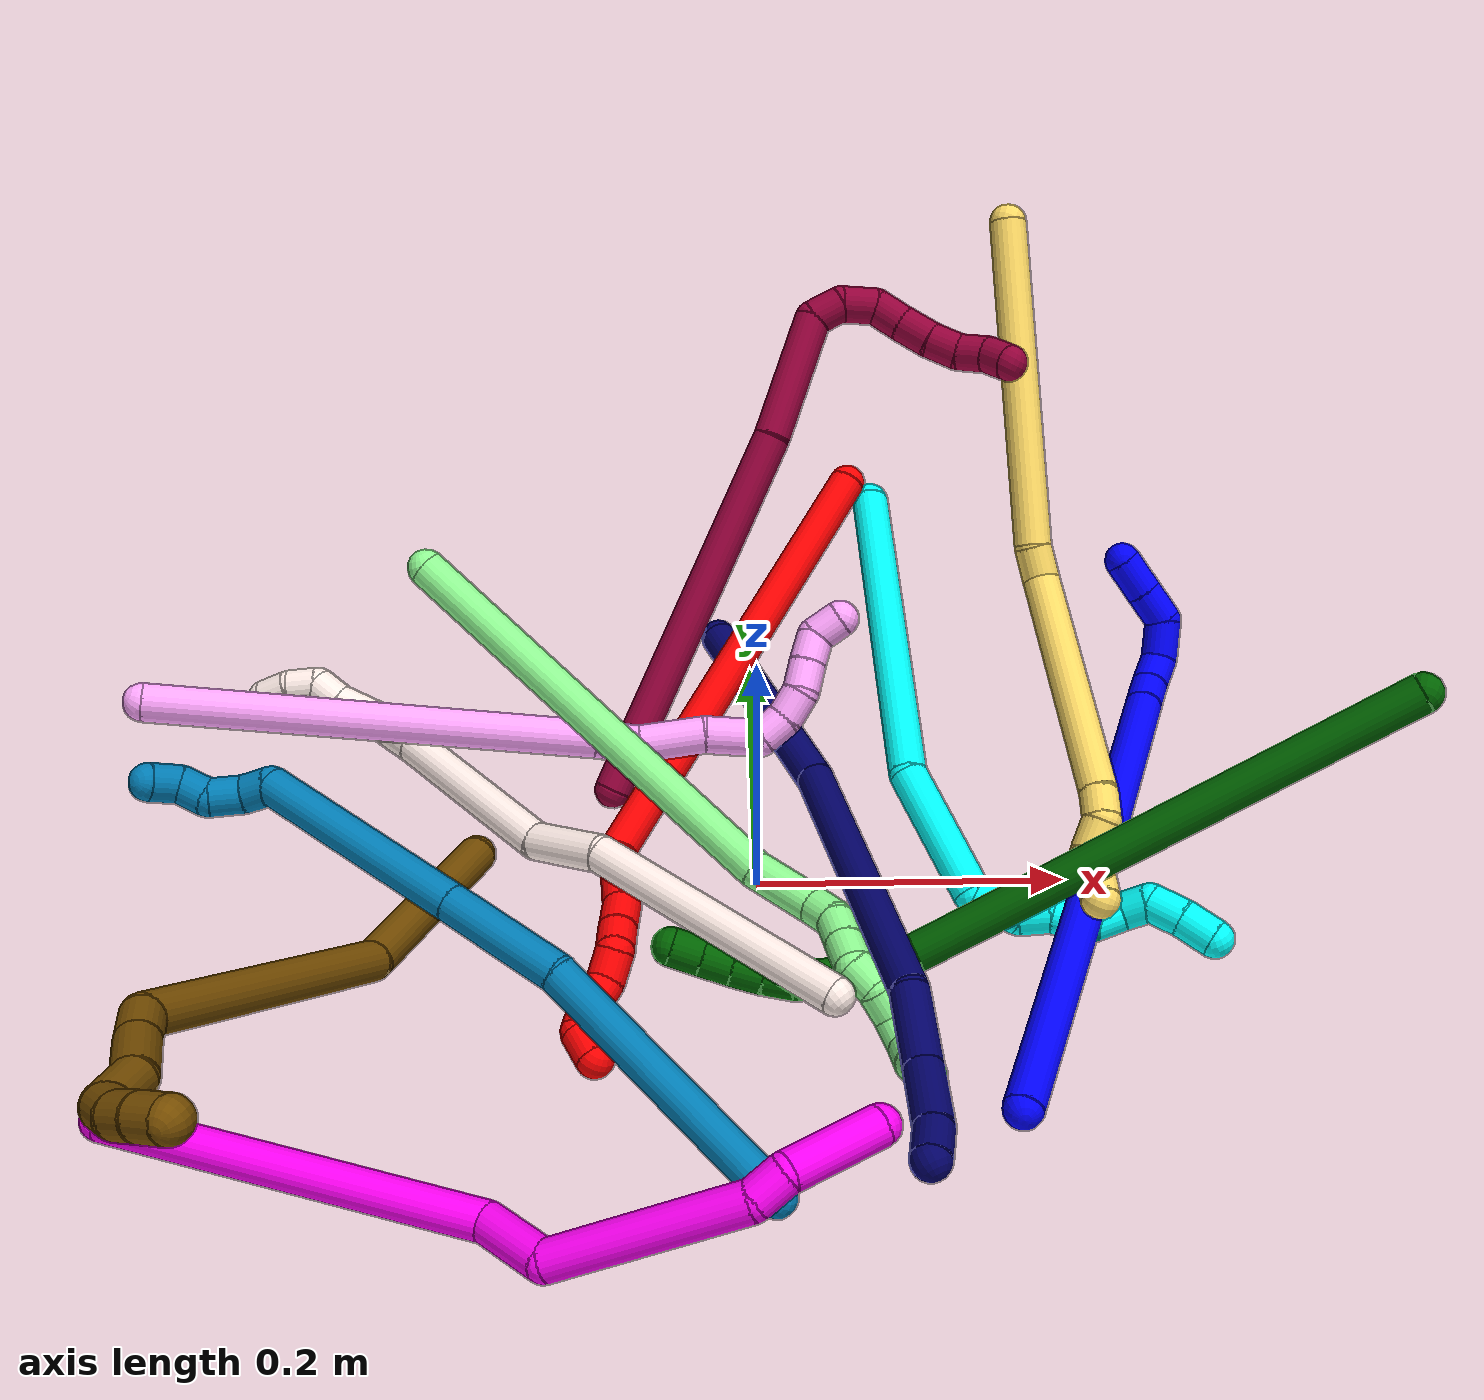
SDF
<sdf version="1.7">
 <world name="default">
  <plugin name="TubeGeneratorPlugin" filename="libtube_generator_plugin.so"/>
  <model name="photoneo_s_sensor">
   <static>1</static>
   <pose>0 0 2 1.57079 1.57079 3.14159</pose>
   <link name="link">
    <inertial><mass>0.1</mass></inertial>
    <sensor name="sensor" type="depth">
     <update_rate>30</update_rate>
     <camera>
      <horizontal_fov>1.22</horizontal_fov>
      <image><width>1920</width><height>1200</height><format>B8G8R8</format></image>
      <clip><near>0.1</near><far>4</far></clip>
      <depth_camera><output>points</output></depth_camera>
     </camera>
     <plugin name="camera_plugin" filename="libgazebo_ros_depth_camera.so">
      <baseline>0.2</baseline>
      <alwaysOn>1</alwaysOn>
      <updateRate>0.0</updateRate>
      <cameraName>camera_ir</cameraName>
      <imageTopicName>/camera/color/image_raw</imageTopicName>
      <cameraInfoTopicName>/camera/color/camera_info</cameraInfoTopicName>
      <depthImageTopicName>/camera/depth/image_raw</depthImageTopicName>
      <depthImageCameraInfoTopicName>/camera/depth/camera_info</depthImageCameraInfoTopicName>
      <pointCloudTopicName>/camera/depth/points</pointCloudTopicName>
      <frameName>fr_optical</frameName>
      <pointCloudCutoff>0.1</pointCloudCutoff>
      <pointCloudCutoffMax>2.0</pointCloudCutoffMax>
      <distortionK1>0</distortionK1>
      <distortionK2>0</distortionK2>
      <distortionK3>0</distortionK3>
      <distortionT1>0</distortionT1>
      <distortionT2>0</distortionT2>
      <CxPrime>0</CxPrime>
      <Cx>0</Cx>
      <Cy>0</Cy>
      <focalLength>0</focalLength>
      <hackBaseline>0</hackBaseline>
     </plugin>
    </sensor>
   </link>
  </model>
  <gravity>0 0 -9.8</gravity>
  <magnetic_field>6e-06 2.3e-05 -4.2e-05</magnetic_field>
  <atmosphere type="adiabatic"/>
  <physics name="default_physics" default="0" type="ode">
   <max_step_size>0.003</max_step_size>
   <real_time_factor>1</real_time_factor>
   <real_time_update_rate>1000</real_time_update_rate>
   <max_contacts>10000</max_contacts>
   <ode>
    <solver>
     <type>quick</type>
     <iters>100</iters>
     <sor>1.3</sor>
     <use_dynamic_moi_rescaling>0</use_dynamic_moi_rescaling>
    </solver>
    <constraints>
     <contact_max_correcting_vel>0</contact_max_correcting_vel>
     <contact_surface_layer>0.001</contact_surface_layer>
     <cfm>0</cfm>
     <erp>0.2</erp>
    </constraints>
   </ode>
  </physics>
  <scene><ambient>0.4 0.4 0.4 1</ambient><background>0.7 0.7 0.7 1</background><shadows>0</shadows></scene>
  <audio><device>default</device></audio>
  <spherical_coordinates>
   <surface_model>EARTH_WGS84</surface_model>
   <latitude_deg>0</latitude_deg>
   <longitude_deg>0</longitude_deg>
   <elevation>0</elevation>
   <heading_deg>0</heading_deg>
  </spherical_coordinates>
  <model name="bin">
   <static>1</static>
   <link name="bottom">
    <collision name="collision-bottom">
     <pose>0 0 -0.01 0 -0 0</pose>
     <geometry><box><size>0.8 0.6 0.02</size></box></geometry>
     <surface>
      <friction><ode><mu>100</mu><mu2>100</mu2></ode></friction>
      <contact><collide_bitmask>65535</collide_bitmask></contact>
     </surface>
    </collision>
   </link>
   <link name="west_wall">
    <collision name="collision-west_wall">
     <pose>-0.41 0 0.1 0 -0 0</pose>
     <geometry><box><size>0.02 0.6 0.2</size></box></geometry>
     <surface>
      <friction><ode><mu>100</mu><mu2>100</mu2></ode></friction>
      <contact><collide_bitmask>65535</collide_bitmask></contact>
     </surface>
    </collision>
   </link>
   <link name="east_wall">
    <collision name="collision-east_wall">
     <pose>0.41 0 0.1 0 -0 0</pose>
     <geometry><box><size>0.02 0.6 0.2</size></box></geometry>
     <surface>
      <friction><ode><mu>100</mu><mu2>100</mu2></ode></friction>
      <contact><collide_bitmask>65535</collide_bitmask></contact>
     </surface>
    </collision>
   </link>
   <link name="south_wall">
    <collision name="collision-south_wall">
     <pose>0 -0.31 0.1 0 -0 0</pose>
     <geometry><box><size>0.8 0.02 0.2</size></box></geometry>
     <surface>
      <friction><ode><mu>100</mu><mu2>100</mu2></ode></friction>
      <contact><collide_bitmask>65535</collide_bitmask></contact>
     </surface>
    </collision>
   </link>
   <link name="north_wall">
    <collision name="collision-north_wall">
     <pose>0 0.31 0.1 0 -0 0</pose>
     <geometry><box><size>0.8 0.02 0.2</size></box></geometry>
     <surface>
      <friction><ode><mu>100</mu><mu2>100</mu2></ode></friction>
      <contact><collide_bitmask>65535</collide_bitmask></contact>
     </surface>
    </collision>
   </link>
  </model>
  <model name="1">
   <static>0</static>
   <link name="1">
    <collision name="collision-cylinder-e_1_1_4">
     <pose>0.017585 0.034183 -0.079534 -2.73567 0.200402 -0.90886</pose>
     <geometry><cylinder><radius>0.0125</radius><length>0.176673</length></cylinder></geometry>
     <surface>
      <friction><ode><mu>1.16</mu><mu2>1.16</mu2><slip1>0</slip1><slip2>0</slip2></ode></friction>
      <contact><ode><kp>1e+06</kp><kd>1</kd><max_vel>0</max_vel><min_depth>0.001</min_depth></ode></contact>
     </surface>
    </collision>
    <visual name="visual-cylinder-e_1_1_4">
     <pose>0.017585 0.034183 -0.079534 -2.73567 0.200402 -0.90886</pose>
     <geometry><cylinder><radius>0.0125</radius><length>0.176673</length></cylinder></geometry>
     <material><ambient>0 0 1 1</ambient></material>
    </visual>
    <collision name="collision-cylinder-e_2_4_5">
     <pose>0.054802 0.098646 -0.250079 -2.82042 0.201903 -1.1177</pose>
     <geometry><cylinder><radius>0.0125</radius><length>0.19581</length></cylinder></geometry>
     <surface>
      <friction><ode><mu>1.16</mu><mu2>1.16</mu2><slip1>0</slip1><slip2>0</slip2></ode></friction>
      <contact><ode><kp>1e+06</kp><kd>1</kd><max_vel>0</max_vel><min_depth>0.001</min_depth></ode></contact>
     </surface>
    </collision>
    <visual name="visual-cylinder-e_2_4_5">
     <pose>0.054802 0.098646 -0.250079 -2.82042 0.201903 -1.1177</pose>
     <geometry><cylinder><radius>0.0125</radius><length>0.19581</length></cylinder></geometry>
     <material><ambient>0 0 1 1</ambient></material>
    </visual>
    <collision name="collision-cylinder-e_3_5_6">
     <pose>0.076947 0.132714 -0.352514 -2.82135 0.205731 -1.13746</pose>
     <geometry><cylinder><radius>0.0125</radius><length>0.024589</length></cylinder></geometry>
     <surface>
      <friction><ode><mu>1.16</mu><mu2>1.16</mu2><slip1>0</slip1><slip2>0</slip2></ode></friction>
      <contact><ode><kp>1e+06</kp><kd>1</kd><max_vel>0</max_vel><min_depth>0.001</min_depth></ode></contact>
     </surface>
    </collision>
    <visual name="visual-cylinder-e_3_5_6">
     <pose>0.076947 0.132714 -0.352514 -2.82135 0.205731 -1.13746</pose>
     <geometry><cylinder><radius>0.0125</radius><length>0.024589</length></cylinder></geometry>
     <material><ambient>0 0 1 1</ambient></material>
    </visual>
    <collision name="collision-cylinder-e_4_6_7">
     <pose>0.081722 0.143566 -0.37281 -2.46918 0.19701 -0.551176</pose>
     <geometry><cylinder><radius>0.0125</radius><length>0.02313</length></cylinder></geometry>
     <surface>
      <friction><ode><mu>1.16</mu><mu2>1.16</mu2><slip1>0</slip1><slip2>0</slip2></ode></friction>
      <contact><ode><kp>1e+06</kp><kd>1</kd><max_vel>0</max_vel><min_depth>0.001</min_depth></ode></contact>
     </surface>
    </collision>
    <visual name="visual-cylinder-e_4_6_7">
     <pose>0.081722 0.143566 -0.37281 -2.46918 0.19701 -0.551176</pose>
     <geometry><cylinder><radius>0.0125</radius><length>0.02313</length></cylinder></geometry>
     <material><ambient>0 0 1 1</ambient></material>
    </visual>
    <collision name="collision-cylinder-e_5_7_8">
     <pose>0.081464 0.163594 -0.386623 -1.93493 -0.179819 0.260198</pose>
     <geometry><cylinder><radius>0.0125</radius><length>0.028201</length></cylinder></geometry>
     <surface>
      <friction><ode><mu>1.16</mu><mu2>1.16</mu2><slip1>0</slip1><slip2>0</slip2></ode></friction>
      <contact><ode><kp>1e+06</kp><kd>1</kd><max_vel>0</max_vel><min_depth>0.001</min_depth></ode></contact>
     </surface>
    </collision>
    <visual name="visual-cylinder-e_5_7_8">
     <pose>0.081464 0.163594 -0.386623 -1.93493 -0.179819 0.260198</pose>
     <geometry><cylinder><radius>0.0125</radius><length>0.028201</length></cylinder></geometry>
     <material><ambient>0 0 1 1</ambient></material>
    </visual>
    <collision name="collision-cylinder-e_6_8_9">
     <pose>0.069244 0.183883 -0.393903 -1.87991 -0.900366 1.16906</pose>
     <geometry><cylinder><radius>0.0125</radius><length>0.024755</length></cylinder></geometry>
     <surface>
      <friction><ode><mu>1.16</mu><mu2>1.16</mu2><slip1>0</slip1><slip2>0</slip2></ode></friction>
      <contact><ode><kp>1e+06</kp><kd>1</kd><max_vel>0</max_vel><min_depth>0.001</min_depth></ode></contact>
     </surface>
    </collision>
    <visual name="visual-cylinder-e_6_8_9">
     <pose>0.069244 0.183883 -0.393903 -1.87991 -0.900366 1.16906</pose>
     <geometry><cylinder><radius>0.0125</radius><length>0.024755</length></cylinder></geometry>
     <material><ambient>0 0 1 1</ambient></material>
    </visual>
    <collision name="collision-cylinder-e_7_9_2">
     <pose>0.049068 0.199212 -0.398754 -1.87489 -0.8957 1.15874</pose>
     <geometry><cylinder><radius>0.0125</radius><length>0.026842</length></cylinder></geometry>
     <surface>
      <friction><ode><mu>1.16</mu><mu2>1.16</mu2><slip1>0</slip1><slip2>0</slip2></ode></friction>
      <contact><ode><kp>1e+06</kp><kd>1</kd><max_vel>0</max_vel><min_depth>0.001</min_depth></ode></contact>
     </surface>
    </collision>
    <visual name="visual-cylinder-e_7_9_2">
     <pose>0.049068 0.199212 -0.398754 -1.87489 -0.8957 1.15874</pose>
     <geometry><cylinder><radius>0.0125</radius><length>0.026842</length></cylinder></geometry>
     <material><ambient>0 0 1 1</ambient></material>
    </visual>
    <collision name="collision-sphere-2">
     <pose>0.038591 0.207215 -0.401266 0 -0 0</pose>
     <geometry><sphere><radius>0.0125</radius></sphere></geometry>
     <surface>
      <friction><ode><mu>1.16</mu><mu2>1.16</mu2><slip1>0</slip1><slip2>0</slip2></ode></friction>
      <contact><ode><kp>1e+06</kp><kd>1</kd><max_vel>0</max_vel><min_depth>0.001</min_depth></ode></contact>
     </surface>
    </collision>
    <visual name="visual-sphere-2">
     <pose>0.038591 0.207215 -0.401266 0 -0 0</pose>
     <geometry><sphere><radius>0.0125</radius></sphere></geometry>
     <material><ambient>0 0 1 1</ambient></material>
    </visual>
    <collision name="collision-sphere-9">
     <pose>0.059545 0.191209 -0.396243 0 -0 0</pose>
     <geometry><sphere><radius>0.0125</radius></sphere></geometry>
     <surface>
      <friction><ode><mu>1.16</mu><mu2>1.16</mu2><slip1>0</slip1><slip2>0</slip2></ode></friction>
      <contact><ode><kp>1e+06</kp><kd>1</kd><max_vel>0</max_vel><min_depth>0.001</min_depth></ode></contact>
     </surface>
    </collision>
    <visual name="visual-sphere-9">
     <pose>0.059545 0.191209 -0.396243 0 -0 0</pose>
     <geometry><sphere><radius>0.0125</radius></sphere></geometry>
     <material><ambient>0 0 1 1</ambient></material>
    </visual>
    <collision name="collision-sphere-4">
     <pose>0.035169 0.068367 -0.159068 0 -0 0</pose>
     <geometry><sphere><radius>0.0125</radius></sphere></geometry>
     <surface>
      <friction><ode><mu>1.16</mu><mu2>1.16</mu2><slip1>0</slip1><slip2>0</slip2></ode></friction>
      <contact><ode><kp>1e+06</kp><kd>1</kd><max_vel>0</max_vel><min_depth>0.001</min_depth></ode></contact>
     </surface>
    </collision>
    <visual name="visual-sphere-4">
     <pose>0.035169 0.068367 -0.159068 0 -0 0</pose>
     <geometry><sphere><radius>0.0125</radius></sphere></geometry>
     <material><ambient>0 0 1 1</ambient></material>
    </visual>
    <collision name="collision-sphere-1">
     <geometry><sphere><radius>0.0125</radius></sphere></geometry>
     <surface>
      <friction><ode><mu>1.16</mu><mu2>1.16</mu2><slip1>0</slip1><slip2>0</slip2></ode></friction>
      <contact><ode><kp>1e+06</kp><kd>1</kd><max_vel>0</max_vel><min_depth>0.001</min_depth></ode></contact>
     </surface>
    </collision>
    <visual name="visual-sphere-1">
     <geometry><sphere><radius>0.0125</radius></sphere></geometry>
     <material><ambient>0 0 1 1</ambient></material>
    </visual>
    <collision name="collision-sphere-8">
     <pose>0.078942 0.176557 -0.391564 0 -0 0</pose>
     <geometry><sphere><radius>0.0125</radius></sphere></geometry>
     <surface>
      <friction><ode><mu>1.16</mu><mu2>1.16</mu2><slip1>0</slip1><slip2>0</slip2></ode></friction>
      <contact><ode><kp>1e+06</kp><kd>1</kd><max_vel>0</max_vel><min_depth>0.001</min_depth></ode></contact>
     </surface>
    </collision>
    <visual name="visual-sphere-8">
     <pose>0.078942 0.176557 -0.391564 0 -0 0</pose>
     <geometry><sphere><radius>0.0125</radius></sphere></geometry>
     <material><ambient>0 0 1 1</ambient></material>
    </visual>
    <collision name="collision-sphere-5">
     <pose>0.074436 0.128925 -0.341091 0 -0 0</pose>
     <geometry><sphere><radius>0.0125</radius></sphere></geometry>
     <surface>
      <friction><ode><mu>1.16</mu><mu2>1.16</mu2><slip1>0</slip1><slip2>0</slip2></ode></friction>
      <contact><ode><kp>1e+06</kp><kd>1</kd><max_vel>0</max_vel><min_depth>0.001</min_depth></ode></contact>
     </surface>
    </collision>
    <visual name="visual-sphere-5">
     <pose>0.074436 0.128925 -0.341091 0 -0 0</pose>
     <geometry><sphere><radius>0.0125</radius></sphere></geometry>
     <material><ambient>0 0 1 1</ambient></material>
    </visual>
    <collision name="collision-sphere-6">
     <pose>0.079459 0.136502 -0.363937 0 -0 0</pose>
     <geometry><sphere><radius>0.0125</radius></sphere></geometry>
     <surface>
      <friction><ode><mu>1.16</mu><mu2>1.16</mu2><slip1>0</slip1><slip2>0</slip2></ode></friction>
      <contact><ode><kp>1e+06</kp><kd>1</kd><max_vel>0</max_vel><min_depth>0.001</min_depth></ode></contact>
     </surface>
    </collision>
    <visual name="visual-sphere-6">
     <pose>0.079459 0.136502 -0.363937 0 -0 0</pose>
     <geometry><sphere><radius>0.0125</radius></sphere></geometry>
     <material><ambient>0 0 1 1</ambient></material>
    </visual>
    <collision name="collision-sphere-7">
     <pose>0.083986 0.15063 -0.381682 0 -0 0</pose>
     <geometry><sphere><radius>0.0125</radius></sphere></geometry>
     <surface>
      <friction><ode><mu>1.16</mu><mu2>1.16</mu2><slip1>0</slip1><slip2>0</slip2></ode></friction>
      <contact><ode><kp>1e+06</kp><kd>1</kd><max_vel>0</max_vel><min_depth>0.001</min_depth></ode></contact>
     </surface>
    </collision>
    <visual name="visual-sphere-7">
     <pose>0.083986 0.15063 -0.381682 0 -0 0</pose>
     <geometry><sphere><radius>0.0125</radius></sphere></geometry>
     <material><ambient>0 0 1 1</ambient></material>
    </visual>
    <inertial>
     <pose>0.045897 0.092904 -0.223336 0 -0 0</pose>
     <mass>0.5</mass>
     <inertia>
      <ixx>-0.000356</ixx>
      <ixy>0</ixy>
      <ixz>0</ixz>
      <iyy>-0.001363</iyy>
      <iyz>0</iyz>
      <izz>-0.000632</izz>
     </inertia>
    </inertial>
   </link>
   <pose>0.148053 -0.205701 0.042931 1.1837 0.25726 -0.151642</pose>
  </model>
  <model name="2">
   <static>0</static>
   <link name="2">
    <collision name="collision-cylinder-e_1_1_4">
     <pose>-0.065632 -0.099158 -0.11053 2.41037 -0.416177 -1.00806</pose>
     <geometry><cylinder><radius>0.0125</radius><length>0.324695</length></cylinder></geometry>
     <surface>
      <friction><ode><mu>1.16</mu><mu2>1.16</mu2><slip1>0</slip1><slip2>0</slip2></ode></friction>
      <contact><ode><kp>1e+06</kp><kd>1</kd><max_vel>0</max_vel><min_depth>0.001</min_depth></ode></contact>
     </surface>
    </collision>
    <visual name="visual-cylinder-e_1_1_4">
     <pose>-0.065632 -0.099158 -0.11053 2.41037 -0.416177 -1.00806</pose>
     <geometry><cylinder><radius>0.0125</radius><length>0.324695</length></cylinder></geometry>
     <material><ambient>1 0 0 1</ambient></material>
    </visual>
    <collision name="collision-cylinder-e_2_4_5">
     <pose>-0.132399 -0.210656 -0.222706 1.70341 -0.090958 -0.103876</pose>
     <geometry><cylinder><radius>0.0125</radius><length>0.025002</length></cylinder></geometry>
     <surface>
      <friction><ode><mu>1.16</mu><mu2>1.16</mu2><slip1>0</slip1><slip2>0</slip2></ode></friction>
      <contact><ode><kp>1e+06</kp><kd>1</kd><max_vel>0</max_vel><min_depth>0.001</min_depth></ode></contact>
     </surface>
    </collision>
    <visual name="visual-cylinder-e_2_4_5">
     <pose>-0.132399 -0.210656 -0.222706 1.70341 -0.090958 -0.103876</pose>
     <geometry><cylinder><radius>0.0125</radius><length>0.025002</length></cylinder></geometry>
     <material><ambient>1 0 0 1</ambient></material>
    </visual>
    <collision name="collision-cylinder-e_3_5_6">
     <pose>-0.135058 -0.235643 -0.226225 1.71788 -0.118668 -0.137489</pose>
     <geometry><cylinder><radius>0.0125</radius><length>0.025751</length></cylinder></geometry>
     <surface>
      <friction><ode><mu>1.16</mu><mu2>1.16</mu2><slip1>0</slip1><slip2>0</slip2></ode></friction>
      <contact><ode><kp>1e+06</kp><kd>1</kd><max_vel>0</max_vel><min_depth>0.001</min_depth></ode></contact>
     </surface>
    </collision>
    <visual name="visual-cylinder-e_3_5_6">
     <pose>-0.135058 -0.235643 -0.226225 1.71788 -0.118668 -0.137489</pose>
     <geometry><cylinder><radius>0.0125</radius><length>0.025751</length></cylinder></geometry>
     <material><ambient>1 0 0 1</ambient></material>
    </visual>
    <collision name="collision-cylinder-e_4_6_7">
     <pose>-0.140235 -0.259613 -0.229545 1.69783 -0.309681 -0.35094</pose>
     <geometry><cylinder><radius>0.0125</radius><length>0.02397</length></cylinder></geometry>
     <surface>
      <friction><ode><mu>1.16</mu><mu2>1.16</mu2><slip1>0</slip1><slip2>0</slip2></ode></friction>
      <contact><ode><kp>1e+06</kp><kd>1</kd><max_vel>0</max_vel><min_depth>0.001</min_depth></ode></contact>
     </surface>
    </collision>
    <visual name="visual-cylinder-e_4_6_7">
     <pose>-0.140235 -0.259613 -0.229545 1.69783 -0.309681 -0.35094</pose>
     <geometry><cylinder><radius>0.0125</radius><length>0.02397</length></cylinder></geometry>
     <material><ambient>1 0 0 1</ambient></material>
    </visual>
    <collision name="collision-cylinder-e_5_7_8">
     <pose>-0.146526 -0.280599 -0.232405 1.71612 -0.263877 -0.304713</pose>
     <geometry><cylinder><radius>0.0125</radius><length>0.020232</length></cylinder></geometry>
     <surface>
      <friction><ode><mu>1.16</mu><mu2>1.16</mu2><slip1>0</slip1><slip2>0</slip2></ode></friction>
      <contact><ode><kp>1e+06</kp><kd>1</kd><max_vel>0</max_vel><min_depth>0.001</min_depth></ode></contact>
     </surface>
    </collision>
    <visual name="visual-cylinder-e_5_7_8">
     <pose>-0.146526 -0.280599 -0.232405 1.71612 -0.263877 -0.304713</pose>
     <geometry><cylinder><radius>0.0125</radius><length>0.020232</length></cylinder></geometry>
     <material><ambient>1 0 0 1</ambient></material>
    </visual>
    <collision name="collision-cylinder-e_6_8_9">
     <pose>-0.150354 -0.296393 -0.241801 2.48654 -0.117641 -0.343232</pose>
     <geometry><cylinder><radius>0.0125</radius><length>0.020268</length></cylinder></geometry>
     <surface>
      <friction><ode><mu>1.16</mu><mu2>1.16</mu2><slip1>0</slip1><slip2>0</slip2></ode></friction>
      <contact><ode><kp>1e+06</kp><kd>1</kd><max_vel>0</max_vel><min_depth>0.001</min_depth></ode></contact>
     </surface>
    </collision>
    <visual name="visual-cylinder-e_6_8_9">
     <pose>-0.150354 -0.296393 -0.241801 2.48654 -0.117641 -0.343232</pose>
     <geometry><cylinder><radius>0.0125</radius><length>0.020268</length></cylinder></geometry>
     <material><ambient>1 0 0 1</ambient></material>
    </visual>
    <collision name="collision-cylinder-e_7_9_10">
     <pose>-0.156544 -0.309752 -0.254629 2.16155 -0.521532 -0.927693</pose>
     <geometry><cylinder><radius>0.0125</radius><length>0.020075</length></cylinder></geometry>
     <surface>
      <friction><ode><mu>1.16</mu><mu2>1.16</mu2><slip1>0</slip1><slip2>0</slip2></ode></friction>
      <contact><ode><kp>1e+06</kp><kd>1</kd><max_vel>0</max_vel><min_depth>0.001</min_depth></ode></contact>
     </surface>
    </collision>
    <visual name="visual-cylinder-e_7_9_10">
     <pose>-0.156544 -0.309752 -0.254629 2.16155 -0.521532 -0.927693</pose>
     <geometry><cylinder><radius>0.0125</radius><length>0.020075</length></cylinder></geometry>
     <material><ambient>1 0 0 1</ambient></material>
    </visual>
    <collision name="collision-cylinder-e_8_10_11">
     <pose>-0.165001 -0.325657 -0.263058 1.96225 -0.352734 -0.52064</pose>
     <geometry><cylinder><radius>0.0125</radius><length>0.020006</length></cylinder></geometry>
     <surface>
      <friction><ode><mu>1.16</mu><mu2>1.16</mu2><slip1>0</slip1><slip2>0</slip2></ode></friction>
      <contact><ode><kp>1e+06</kp><kd>1</kd><max_vel>0</max_vel><min_depth>0.001</min_depth></ode></contact>
     </surface>
    </collision>
    <visual name="visual-cylinder-e_8_10_11">
     <pose>-0.165001 -0.325657 -0.263058 1.96225 -0.352734 -0.52064</pose>
     <geometry><cylinder><radius>0.0125</radius><length>0.020006</length></cylinder></geometry>
     <material><ambient>1 0 0 1</ambient></material>
    </visual>
    <collision name="collision-cylinder-e_9_11_2">
     <pose>-0.165033 -0.343641 -0.267935 1.70917 0.349437 0.40018</pose>
     <geometry><cylinder><radius>0.0125</radius><length>0.020001</length></cylinder></geometry>
     <surface>
      <friction><ode><mu>1.16</mu><mu2>1.16</mu2><slip1>0</slip1><slip2>0</slip2></ode></friction>
      <contact><ode><kp>1e+06</kp><kd>1</kd><max_vel>0</max_vel><min_depth>0.001</min_depth></ode></contact>
     </surface>
    </collision>
    <visual name="visual-cylinder-e_9_11_2">
     <pose>-0.165033 -0.343641 -0.267935 1.70917 0.349437 0.40018</pose>
     <geometry><cylinder><radius>0.0125</radius><length>0.020001</length></cylinder></geometry>
     <material><ambient>1 0 0 1</ambient></material>
    </visual>
    <collision name="collision-sphere-2">
     <pose>-0.161609 -0.352947 -0.269232 0 -0 0</pose>
     <geometry><sphere><radius>0.0125</radius></sphere></geometry>
     <surface>
      <friction><ode><mu>1.16</mu><mu2>1.16</mu2><slip1>0</slip1><slip2>0</slip2></ode></friction>
      <contact><ode><kp>1e+06</kp><kd>1</kd><max_vel>0</max_vel><min_depth>0.001</min_depth></ode></contact>
     </surface>
    </collision>
    <visual name="visual-sphere-2">
     <pose>-0.161609 -0.352947 -0.269232 0 -0 0</pose>
     <geometry><sphere><radius>0.0125</radius></sphere></geometry>
     <material><ambient>1 0 0 1</ambient></material>
    </visual>
    <collision name="collision-sphere-11">
     <pose>-0.168456 -0.334334 -0.266639 0 -0 0</pose>
     <geometry><sphere><radius>0.0125</radius></sphere></geometry>
     <surface>
      <friction><ode><mu>1.16</mu><mu2>1.16</mu2><slip1>0</slip1><slip2>0</slip2></ode></friction>
      <contact><ode><kp>1e+06</kp><kd>1</kd><max_vel>0</max_vel><min_depth>0.001</min_depth></ode></contact>
     </surface>
    </collision>
    <visual name="visual-sphere-11">
     <pose>-0.168456 -0.334334 -0.266639 0 -0 0</pose>
     <geometry><sphere><radius>0.0125</radius></sphere></geometry>
     <material><ambient>1 0 0 1</ambient></material>
    </visual>
    <collision name="collision-sphere-10">
     <pose>-0.161545 -0.316981 -0.259477 0 -0 0</pose>
     <geometry><sphere><radius>0.0125</radius></sphere></geometry>
     <surface>
      <friction><ode><mu>1.16</mu><mu2>1.16</mu2><slip1>0</slip1><slip2>0</slip2></ode></friction>
      <contact><ode><kp>1e+06</kp><kd>1</kd><max_vel>0</max_vel><min_depth>0.001</min_depth></ode></contact>
     </surface>
    </collision>
    <visual name="visual-sphere-10">
     <pose>-0.161545 -0.316981 -0.259477 0 -0 0</pose>
     <geometry><sphere><radius>0.0125</radius></sphere></geometry>
     <material><ambient>1 0 0 1</ambient></material>
    </visual>
    <collision name="collision-sphere-9">
     <pose>-0.151544 -0.302524 -0.249782 0 -0 0</pose>
     <geometry><sphere><radius>0.0125</radius></sphere></geometry>
     <surface>
      <friction><ode><mu>1.16</mu><mu2>1.16</mu2><slip1>0</slip1><slip2>0</slip2></ode></friction>
      <contact><ode><kp>1e+06</kp><kd>1</kd><max_vel>0</max_vel><min_depth>0.001</min_depth></ode></contact>
     </surface>
    </collision>
    <visual name="visual-sphere-9">
     <pose>-0.151544 -0.302524 -0.249782 0 -0 0</pose>
     <geometry><sphere><radius>0.0125</radius></sphere></geometry>
     <material><ambient>1 0 0 1</ambient></material>
    </visual>
    <collision name="collision-sphere-4">
     <pose>-0.131263 -0.198316 -0.221059 0 -0 0</pose>
     <geometry><sphere><radius>0.0125</radius></sphere></geometry>
     <surface>
      <friction><ode><mu>1.16</mu><mu2>1.16</mu2><slip1>0</slip1><slip2>0</slip2></ode></friction>
      <contact><ode><kp>1e+06</kp><kd>1</kd><max_vel>0</max_vel><min_depth>0.001</min_depth></ode></contact>
     </surface>
    </collision>
    <visual name="visual-sphere-4">
     <pose>-0.131263 -0.198316 -0.221059 0 -0 0</pose>
     <geometry><sphere><radius>0.0125</radius></sphere></geometry>
     <material><ambient>1 0 0 1</ambient></material>
    </visual>
    <collision name="collision-sphere-1">
     <geometry><sphere><radius>0.0125</radius></sphere></geometry>
     <surface>
      <friction><ode><mu>1.16</mu><mu2>1.16</mu2><slip1>0</slip1><slip2>0</slip2></ode></friction>
      <contact><ode><kp>1e+06</kp><kd>1</kd><max_vel>0</max_vel><min_depth>0.001</min_depth></ode></contact>
     </surface>
    </collision>
    <visual name="visual-sphere-1">
     <geometry><sphere><radius>0.0125</radius></sphere></geometry>
     <material><ambient>1 0 0 1</ambient></material>
    </visual>
    <collision name="collision-sphere-8">
     <pose>-0.149165 -0.290262 -0.23382 0 -0 0</pose>
     <geometry><sphere><radius>0.0125</radius></sphere></geometry>
     <surface>
      <friction><ode><mu>1.16</mu><mu2>1.16</mu2><slip1>0</slip1><slip2>0</slip2></ode></friction>
      <contact><ode><kp>1e+06</kp><kd>1</kd><max_vel>0</max_vel><min_depth>0.001</min_depth></ode></contact>
     </surface>
    </collision>
    <visual name="visual-sphere-8">
     <pose>-0.149165 -0.290262 -0.23382 0 -0 0</pose>
     <geometry><sphere><radius>0.0125</radius></sphere></geometry>
     <material><ambient>1 0 0 1</ambient></material>
    </visual>
    <collision name="collision-sphere-5">
     <pose>-0.133534 -0.222997 -0.224352 0 -0 0</pose>
     <geometry><sphere><radius>0.0125</radius></sphere></geometry>
     <surface>
      <friction><ode><mu>1.16</mu><mu2>1.16</mu2><slip1>0</slip1><slip2>0</slip2></ode></friction>
      <contact><ode><kp>1e+06</kp><kd>1</kd><max_vel>0</max_vel><min_depth>0.001</min_depth></ode></contact>
     </surface>
    </collision>
    <visual name="visual-sphere-5">
     <pose>-0.133534 -0.222997 -0.224352 0 -0 0</pose>
     <geometry><sphere><radius>0.0125</radius></sphere></geometry>
     <material><ambient>1 0 0 1</ambient></material>
    </visual>
    <collision name="collision-sphere-6">
     <pose>-0.136583 -0.24829 -0.228099 0 -0 0</pose>
     <geometry><sphere><radius>0.0125</radius></sphere></geometry>
     <surface>
      <friction><ode><mu>1.16</mu><mu2>1.16</mu2><slip1>0</slip1><slip2>0</slip2></ode></friction>
      <contact><ode><kp>1e+06</kp><kd>1</kd><max_vel>0</max_vel><min_depth>0.001</min_depth></ode></contact>
     </surface>
    </collision>
    <visual name="visual-sphere-6">
     <pose>-0.136583 -0.24829 -0.228099 0 -0 0</pose>
     <geometry><sphere><radius>0.0125</radius></sphere></geometry>
     <material><ambient>1 0 0 1</ambient></material>
    </visual>
    <collision name="collision-sphere-7">
     <pose>-0.143888 -0.270936 -0.230991 0 -0 0</pose>
     <geometry><sphere><radius>0.0125</radius></sphere></geometry>
     <surface>
      <friction><ode><mu>1.16</mu><mu2>1.16</mu2><slip1>0</slip1><slip2>0</slip2></ode></friction>
      <contact><ode><kp>1e+06</kp><kd>1</kd><max_vel>0</max_vel><min_depth>0.001</min_depth></ode></contact>
     </surface>
    </collision>
    <visual name="visual-sphere-7">
     <pose>-0.143888 -0.270936 -0.230991 0 -0 0</pose>
     <geometry><sphere><radius>0.0125</radius></sphere></geometry>
     <material><ambient>1 0 0 1</ambient></material>
    </visual>
    <inertial>
     <pose>-0.094432 -0.16209 -0.156241 0 -0 0</pose>
     <mass>0.5</mass>
     <inertia>
      <ixx>-0.000822</ixx>
      <ixy>0</ixy>
      <ixz>0</ixz>
      <iyy>-0.002733</iyy>
      <iyz>0</iyz>
      <izz>0.002902</izz>
     </inertia>
    </inertial>
   </link>
   <pose>0.07078 0.288031 0.10012 -0.207517 0.51208 0.152343</pose>
  </model>
  <model name="3">
   <static>0</static>
   <link name="3">
    <collision name="collision-cylinder-e_1_1_4">
     <pose>0.049196 -0.089648 -0.062748 2.18148 0.422505 0.78139</pose>
     <geometry><cylinder><radius>0.0125</radius><length>0.239952</length></cylinder></geometry>
     <surface>
      <friction><ode><mu>1.16</mu><mu2>1.16</mu2><slip1>0</slip1><slip2>0</slip2></ode></friction>
      <contact><ode><kp>1e+06</kp><kd>1</kd><max_vel>0</max_vel><min_depth>0.001</min_depth></ode></contact>
     </surface>
    </collision>
    <visual name="visual-cylinder-e_1_1_4">
     <pose>0.049196 -0.089648 -0.062748 2.18148 0.422505 0.78139</pose>
     <geometry><cylinder><radius>0.0125</radius><length>0.239952</length></cylinder></geometry>
     <material><ambient>0.003922 1 0.996078 1</ambient></material>
    </visual>
    <collision name="collision-cylinder-e_2_4_5">
     <pose>0.122801 -0.199264 -0.159077 2.60513 0.55845 1.61304</pose>
     <geometry><cylinder><radius>0.0125</radius><length>0.092136</length></cylinder></geometry>
     <surface>
      <friction><ode><mu>1.16</mu><mu2>1.16</mu2><slip1>0</slip1><slip2>0</slip2></ode></friction>
      <contact><ode><kp>1e+06</kp><kd>1</kd><max_vel>0</max_vel><min_depth>0.001</min_depth></ode></contact>
     </surface>
    </collision>
    <visual name="visual-cylinder-e_2_4_5">
     <pose>0.122801 -0.199264 -0.159077 2.60513 0.55845 1.61304</pose>
     <geometry><cylinder><radius>0.0125</radius><length>0.092136</length></cylinder></geometry>
     <material><ambient>0.003922 1 0.996078 1</ambient></material>
    </visual>
    <collision name="collision-cylinder-e_3_5_6">
     <pose>0.157358 -0.213966 -0.204665 -2.7283 0.658594 -2.0411</pose>
     <geometry><cylinder><radius>0.0125</radius><length>0.033159</length></cylinder></geometry>
     <surface>
      <friction><ode><mu>1.16</mu><mu2>1.16</mu2><slip1>0</slip1><slip2>0</slip2></ode></friction>
      <contact><ode><kp>1e+06</kp><kd>1</kd><max_vel>0</max_vel><min_depth>0.001</min_depth></ode></contact>
     </surface>
    </collision>
    <visual name="visual-cylinder-e_3_5_6">
     <pose>0.157358 -0.213966 -0.204665 -2.7283 0.658594 -2.0411</pose>
     <geometry><cylinder><radius>0.0125</radius><length>0.033159</length></cylinder></geometry>
     <material><ambient>0.003922 1 0.996078 1</ambient></material>
    </visual>
    <collision name="collision-cylinder-e_4_6_7">
     <pose>0.175978 -0.203719 -0.219014 -2.01018 0.994743 -1.41484</pose>
     <geometry><cylinder><radius>0.0125</radius><length>0.020208</length></cylinder></geometry>
     <surface>
      <friction><ode><mu>1.16</mu><mu2>1.16</mu2><slip1>0</slip1><slip2>0</slip2></ode></friction>
      <contact><ode><kp>1e+06</kp><kd>1</kd><max_vel>0</max_vel><min_depth>0.001</min_depth></ode></contact>
     </surface>
    </collision>
    <visual name="visual-cylinder-e_4_6_7">
     <pose>0.175978 -0.203719 -0.219014 -2.01018 0.994743 -1.41484</pose>
     <geometry><cylinder><radius>0.0125</radius><length>0.020208</length></cylinder></geometry>
     <material><ambient>0.003922 1 0.996078 1</ambient></material>
    </visual>
    <collision name="collision-cylinder-e_5_7_8">
     <pose>0.193498 -0.194007 -0.228359 -2.5475 0.819421 -1.91366</pose>
     <geometry><cylinder><radius>0.0125</radius><length>0.024761</length></cylinder></geometry>
     <surface>
      <friction><ode><mu>1.16</mu><mu2>1.16</mu2><slip1>0</slip1><slip2>0</slip2></ode></friction>
      <contact><ode><kp>1e+06</kp><kd>1</kd><max_vel>0</max_vel><min_depth>0.001</min_depth></ode></contact>
     </surface>
    </collision>
    <visual name="visual-cylinder-e_5_7_8">
     <pose>0.193498 -0.194007 -0.228359 -2.5475 0.819421 -1.91366</pose>
     <geometry><cylinder><radius>0.0125</radius><length>0.024761</length></cylinder></geometry>
     <material><ambient>0.003922 1 0.996078 1</ambient></material>
    </visual>
    <collision name="collision-cylinder-e_6_8_9">
     <pose>0.208136 -0.179231 -0.237585 -1.78858 0.497744 -0.6131</pose>
     <geometry><cylinder><radius>0.0125</radius><length>0.023419</length></cylinder></geometry>
     <surface>
      <friction><ode><mu>1.16</mu><mu2>1.16</mu2><slip1>0</slip1><slip2>0</slip2></ode></friction>
      <contact><ode><kp>1e+06</kp><kd>1</kd><max_vel>0</max_vel><min_depth>0.001</min_depth></ode></contact>
     </surface>
    </collision>
    <visual name="visual-cylinder-e_6_8_9">
     <pose>0.208136 -0.179231 -0.237585 -1.78858 0.497744 -0.6131</pose>
     <geometry><cylinder><radius>0.0125</radius><length>0.023419</length></cylinder></geometry>
     <material><ambient>0.003922 1 0.996078 1</ambient></material>
    </visual>
    <collision name="collision-cylinder-e_7_9_10">
     <pose>0.223193 -0.16541 -0.238613 -1.26414 1.17458 -0.907101</pose>
     <geometry><cylinder><radius>0.0125</radius><length>0.020523</length></cylinder></geometry>
     <surface>
      <friction><ode><mu>1.16</mu><mu2>1.16</mu2><slip1>0</slip1><slip2>0</slip2></ode></friction>
      <contact><ode><kp>1e+06</kp><kd>1</kd><max_vel>0</max_vel><min_depth>0.001</min_depth></ode></contact>
     </surface>
    </collision>
    <visual name="visual-cylinder-e_7_9_10">
     <pose>0.223193 -0.16541 -0.238613 -1.26414 1.17458 -0.907101</pose>
     <geometry><cylinder><radius>0.0125</radius><length>0.020523</length></cylinder></geometry>
     <material><ambient>0.003922 1 0.996078 1</ambient></material>
    </visual>
    <collision name="collision-cylinder-e_8_10_11">
     <pose>0.242114 -0.161138 -0.243757 -3.06353 0.978671 -2.9952</pose>
     <geometry><cylinder><radius>0.0125</radius><length>0.022789</length></cylinder></geometry>
     <surface>
      <friction><ode><mu>1.16</mu><mu2>1.16</mu2><slip1>0</slip1><slip2>0</slip2></ode></friction>
      <contact><ode><kp>1e+06</kp><kd>1</kd><max_vel>0</max_vel><min_depth>0.001</min_depth></ode></contact>
     </surface>
    </collision>
    <visual name="visual-cylinder-e_8_10_11">
     <pose>0.242114 -0.161138 -0.243757 -3.06353 0.978671 -2.9952</pose>
     <geometry><cylinder><radius>0.0125</radius><length>0.022789</length></cylinder></geometry>
     <material><ambient>0.003922 1 0.996078 1</ambient></material>
    </visual>
    <collision name="collision-cylinder-e_9_11_2">
     <pose>0.260461 -0.160967 -0.257425 3.09726 0.881063 3.04761</pose>
     <geometry><cylinder><radius>0.0125</radius><length>0.023054</length></cylinder></geometry>
     <surface>
      <friction><ode><mu>1.16</mu><mu2>1.16</mu2><slip1>0</slip1><slip2>0</slip2></ode></friction>
      <contact><ode><kp>1e+06</kp><kd>1</kd><max_vel>0</max_vel><min_depth>0.001</min_depth></ode></contact>
     </surface>
    </collision>
    <visual name="visual-cylinder-e_9_11_2">
     <pose>0.260461 -0.160967 -0.257425 3.09726 0.881063 3.04761</pose>
     <geometry><cylinder><radius>0.0125</radius><length>0.023054</length></cylinder></geometry>
     <material><ambient>0.003922 1 0.996078 1</ambient></material>
    </visual>
    <collision name="collision-sphere-2">
     <pose>0.269354 -0.161293 -0.264753 0 -0 0</pose>
     <geometry><sphere><radius>0.0125</radius></sphere></geometry>
     <surface>
      <friction><ode><mu>1.16</mu><mu2>1.16</mu2><slip1>0</slip1><slip2>0</slip2></ode></friction>
      <contact><ode><kp>1e+06</kp><kd>1</kd><max_vel>0</max_vel><min_depth>0.001</min_depth></ode></contact>
     </surface>
    </collision>
    <visual name="visual-sphere-2">
     <pose>0.269354 -0.161293 -0.264753 0 -0 0</pose>
     <geometry><sphere><radius>0.0125</radius></sphere></geometry>
     <material><ambient>0.003922 1 0.996078 1</ambient></material>
    </visual>
    <collision name="collision-sphere-11">
     <pose>0.251569 -0.160642 -0.250098 0 -0 0</pose>
     <geometry><sphere><radius>0.0125</radius></sphere></geometry>
     <surface>
      <friction><ode><mu>1.16</mu><mu2>1.16</mu2><slip1>0</slip1><slip2>0</slip2></ode></friction>
      <contact><ode><kp>1e+06</kp><kd>1</kd><max_vel>0</max_vel><min_depth>0.001</min_depth></ode></contact>
     </surface>
    </collision>
    <visual name="visual-sphere-11">
     <pose>0.251569 -0.160642 -0.250098 0 -0 0</pose>
     <geometry><sphere><radius>0.0125</radius></sphere></geometry>
     <material><ambient>0.003922 1 0.996078 1</ambient></material>
    </visual>
    <collision name="collision-sphere-10">
     <pose>0.23266 -0.161634 -0.237417 0 -0 0</pose>
     <geometry><sphere><radius>0.0125</radius></sphere></geometry>
     <surface>
      <friction><ode><mu>1.16</mu><mu2>1.16</mu2><slip1>0</slip1><slip2>0</slip2></ode></friction>
      <contact><ode><kp>1e+06</kp><kd>1</kd><max_vel>0</max_vel><min_depth>0.001</min_depth></ode></contact>
     </surface>
    </collision>
    <visual name="visual-sphere-10">
     <pose>0.23266 -0.161634 -0.237417 0 -0 0</pose>
     <geometry><sphere><radius>0.0125</radius></sphere></geometry>
     <material><ambient>0.003922 1 0.996078 1</ambient></material>
    </visual>
    <collision name="collision-sphere-9">
     <pose>0.213726 -0.169185 -0.239808 0 -0 0</pose>
     <geometry><sphere><radius>0.0125</radius></sphere></geometry>
     <surface>
      <friction><ode><mu>1.16</mu><mu2>1.16</mu2><slip1>0</slip1><slip2>0</slip2></ode></friction>
      <contact><ode><kp>1e+06</kp><kd>1</kd><max_vel>0</max_vel><min_depth>0.001</min_depth></ode></contact>
     </surface>
    </collision>
    <visual name="visual-sphere-9">
     <pose>0.213726 -0.169185 -0.239808 0 -0 0</pose>
     <geometry><sphere><radius>0.0125</radius></sphere></geometry>
     <material><ambient>0.003922 1 0.996078 1</ambient></material>
    </visual>
    <collision name="collision-sphere-4">
     <pose>0.098391 -0.179296 -0.125496 0 -0 0</pose>
     <geometry><sphere><radius>0.0125</radius></sphere></geometry>
     <surface>
      <friction><ode><mu>1.16</mu><mu2>1.16</mu2><slip1>0</slip1><slip2>0</slip2></ode></friction>
      <contact><ode><kp>1e+06</kp><kd>1</kd><max_vel>0</max_vel><min_depth>0.001</min_depth></ode></contact>
     </surface>
    </collision>
    <visual name="visual-sphere-4">
     <pose>0.098391 -0.179296 -0.125496 0 -0 0</pose>
     <geometry><sphere><radius>0.0125</radius></sphere></geometry>
     <material><ambient>0.003922 1 0.996078 1</ambient></material>
    </visual>
    <collision name="collision-sphere-1">
     <geometry><sphere><radius>0.0125</radius></sphere></geometry>
     <surface>
      <friction><ode><mu>1.16</mu><mu2>1.16</mu2><slip1>0</slip1><slip2>0</slip2></ode></friction>
      <contact><ode><kp>1e+06</kp><kd>1</kd><max_vel>0</max_vel><min_depth>0.001</min_depth></ode></contact>
     </surface>
    </collision>
    <visual name="visual-sphere-1">
     <geometry><sphere><radius>0.0125</radius></sphere></geometry>
     <material><ambient>0.003922 1 0.996078 1</ambient></material>
    </visual>
    <collision name="collision-sphere-8">
     <pose>0.202545 -0.189276 -0.235362 0 -0 0</pose>
     <geometry><sphere><radius>0.0125</radius></sphere></geometry>
     <surface>
      <friction><ode><mu>1.16</mu><mu2>1.16</mu2><slip1>0</slip1><slip2>0</slip2></ode></friction>
      <contact><ode><kp>1e+06</kp><kd>1</kd><max_vel>0</max_vel><min_depth>0.001</min_depth></ode></contact>
     </surface>
    </collision>
    <visual name="visual-sphere-8">
     <pose>0.202545 -0.189276 -0.235362 0 -0 0</pose>
     <geometry><sphere><radius>0.0125</radius></sphere></geometry>
     <material><ambient>0.003922 1 0.996078 1</ambient></material>
    </visual>
    <collision name="collision-sphere-5">
     <pose>0.147212 -0.219232 -0.192657 0 -0 0</pose>
     <geometry><sphere><radius>0.0125</radius></sphere></geometry>
     <surface>
      <friction><ode><mu>1.16</mu><mu2>1.16</mu2><slip1>0</slip1><slip2>0</slip2></ode></friction>
      <contact><ode><kp>1e+06</kp><kd>1</kd><max_vel>0</max_vel><min_depth>0.001</min_depth></ode></contact>
     </surface>
    </collision>
    <visual name="visual-sphere-5">
     <pose>0.147212 -0.219232 -0.192657 0 -0 0</pose>
     <geometry><sphere><radius>0.0125</radius></sphere></geometry>
     <material><ambient>0.003922 1 0.996078 1</ambient></material>
    </visual>
    <collision name="collision-sphere-6">
     <pose>0.167505 -0.2087 -0.216673 0 -0 0</pose>
     <geometry><sphere><radius>0.0125</radius></sphere></geometry>
     <surface>
      <friction><ode><mu>1.16</mu><mu2>1.16</mu2><slip1>0</slip1><slip2>0</slip2></ode></friction>
      <contact><ode><kp>1e+06</kp><kd>1</kd><max_vel>0</max_vel><min_depth>0.001</min_depth></ode></contact>
     </surface>
    </collision>
    <visual name="visual-sphere-6">
     <pose>0.167505 -0.2087 -0.216673 0 -0 0</pose>
     <geometry><sphere><radius>0.0125</radius></sphere></geometry>
     <material><ambient>0.003922 1 0.996078 1</ambient></material>
    </visual>
    <collision name="collision-sphere-7">
     <pose>0.184451 -0.198738 -0.221356 0 -0 0</pose>
     <geometry><sphere><radius>0.0125</radius></sphere></geometry>
     <surface>
      <friction><ode><mu>1.16</mu><mu2>1.16</mu2><slip1>0</slip1><slip2>0</slip2></ode></friction>
      <contact><ode><kp>1e+06</kp><kd>1</kd><max_vel>0</max_vel><min_depth>0.001</min_depth></ode></contact>
     </surface>
    </collision>
    <visual name="visual-sphere-7">
     <pose>0.184451 -0.198738 -0.221356 0 -0 0</pose>
     <geometry><sphere><radius>0.0125</radius></sphere></geometry>
     <material><ambient>0.003922 1 0.996078 1</ambient></material>
    </visual>
    <inertial>
     <pose>0.115323 -0.141722 -0.137061 0 -0 0</pose>
     <mass>0.5</mass>
     <inertia>
      <ixx>0.001565</ixx>
      <ixy>0</ixy>
      <ixz>0</ixz>
      <iyy>0.000618</iyy>
      <iyz>0</iyz>
      <izz>0.000348</izz>
     </inertia>
    </inertial>
   </link>
   <pose>0.087918 0.288517 0.082516 -0.137182 -0.553587 -0.560184</pose>
  </model>
  <model name="4">
   <static>0</static>
   <link name="4">
    <collision name="collision-cylinder-e_1_1_4">
     <pose>0.062809 -0.024404 -0.127542 2.95253 0.450507 2.35695</pose>
     <geometry><cylinder><radius>0.0125</radius><length>0.288496</length></cylinder></geometry>
     <surface>
      <friction><ode><mu>1.16</mu><mu2>1.16</mu2><slip1>0</slip1><slip2>0</slip2></ode></friction>
      <contact><ode><kp>1e+06</kp><kd>1</kd><max_vel>0</max_vel><min_depth>0.001</min_depth></ode></contact>
     </surface>
    </collision>
    <visual name="visual-cylinder-e_1_1_4">
     <pose>0.062809 -0.024404 -0.127542 2.95253 0.450507 2.35695</pose>
     <geometry><cylinder><radius>0.0125</radius><length>0.288496</length></cylinder></geometry>
     <material><ambient>1 0.65098 0.996078 1</ambient></material>
    </visual>
    <collision name="collision-cylinder-e_2_4_5">
     <pose>0.131321 -0.051271 -0.268005 2.95329 0.409139 2.28734</pose>
     <geometry><cylinder><radius>0.0125</radius><length>0.028673</length></cylinder></geometry>
     <surface>
      <friction><ode><mu>1.16</mu><mu2>1.16</mu2><slip1>0</slip1><slip2>0</slip2></ode></friction>
      <contact><ode><kp>1e+06</kp><kd>1</kd><max_vel>0</max_vel><min_depth>0.001</min_depth></ode></contact>
     </surface>
    </collision>
    <visual name="visual-cylinder-e_2_4_5">
     <pose>0.131321 -0.051271 -0.268005 2.95329 0.409139 2.28734</pose>
     <geometry><cylinder><radius>0.0125</radius><length>0.028673</length></cylinder></geometry>
     <material><ambient>1 0.65098 0.996078 1</ambient></material>
    </visual>
    <collision name="collision-cylinder-e_3_5_6">
     <pose>0.151502 -0.057362 -0.297207 2.9223 0.714806 2.56826</pose>
     <geometry><cylinder><radius>0.0125</radius><length>0.044176</length></cylinder></geometry>
     <surface>
      <friction><ode><mu>1.16</mu><mu2>1.16</mu2><slip1>0</slip1><slip2>0</slip2></ode></friction>
      <contact><ode><kp>1e+06</kp><kd>1</kd><max_vel>0</max_vel><min_depth>0.001</min_depth></ode></contact>
     </surface>
    </collision>
    <visual name="visual-cylinder-e_3_5_6">
     <pose>0.151502 -0.057362 -0.297207 2.9223 0.714806 2.56826</pose>
     <geometry><cylinder><radius>0.0125</radius><length>0.044176</length></cylinder></geometry>
     <material><ambient>1 0.65098 0.996078 1</ambient></material>
    </visual>
    <collision name="collision-cylinder-e_4_6_7">
     <pose>0.174929 -0.06508 -0.329278 2.88814 0.501809 2.21896</pose>
     <geometry><cylinder><radius>0.0125</radius><length>0.037208</length></cylinder></geometry>
     <surface>
      <friction><ode><mu>1.16</mu><mu2>1.16</mu2><slip1>0</slip1><slip2>0</slip2></ode></friction>
      <contact><ode><kp>1e+06</kp><kd>1</kd><max_vel>0</max_vel><min_depth>0.001</min_depth></ode></contact>
     </surface>
    </collision>
    <visual name="visual-cylinder-e_4_6_7">
     <pose>0.174929 -0.06508 -0.329278 2.88814 0.501809 2.21896</pose>
     <geometry><cylinder><radius>0.0125</radius><length>0.037208</length></cylinder></geometry>
     <material><ambient>1 0.65098 0.996078 1</ambient></material>
    </visual>
    <collision name="collision-cylinder-e_5_7_8">
     <pose>0.19284 -0.067167 -0.349281 -2.69779 1.09083 -2.42966</pose>
     <geometry><cylinder><radius>0.0125</radius><length>0.020208</length></cylinder></geometry>
     <surface>
      <friction><ode><mu>1.16</mu><mu2>1.16</mu2><slip1>0</slip1><slip2>0</slip2></ode></friction>
      <contact><ode><kp>1e+06</kp><kd>1</kd><max_vel>0</max_vel><min_depth>0.001</min_depth></ode></contact>
     </surface>
    </collision>
    <visual name="visual-cylinder-e_5_7_8">
     <pose>0.19284 -0.067167 -0.349281 -2.69779 1.09083 -2.42966</pose>
     <geometry><cylinder><radius>0.0125</radius><length>0.020208</length></cylinder></geometry>
     <material><ambient>1 0.65098 0.996078 1</ambient></material>
    </visual>
    <collision name="collision-cylinder-e_6_8_9">
     <pose>0.211454 -0.061843 -0.354523 -1.87114 1.22511 -1.523</pose>
     <geometry><cylinder><radius>0.0125</radius><length>0.020517</length></cylinder></geometry>
     <surface>
      <friction><ode><mu>1.16</mu><mu2>1.16</mu2><slip1>0</slip1><slip2>0</slip2></ode></friction>
      <contact><ode><kp>1e+06</kp><kd>1</kd><max_vel>0</max_vel><min_depth>0.001</min_depth></ode></contact>
     </surface>
    </collision>
    <visual name="visual-cylinder-e_6_8_9">
     <pose>0.211454 -0.061843 -0.354523 -1.87114 1.22511 -1.523</pose>
     <geometry><cylinder><radius>0.0125</radius><length>0.020517</length></cylinder></geometry>
     <material><ambient>1 0.65098 0.996078 1</ambient></material>
    </visual>
    <collision name="collision-cylinder-e_7_9_10">
     <pose>0.228743 -0.051833 -0.355225 -1.52213 0.850918 -0.814901</pose>
     <geometry><cylinder><radius>0.0125</radius><length>0.020317</length></cylinder></geometry>
     <surface>
      <friction><ode><mu>1.16</mu><mu2>1.16</mu2><slip1>0</slip1><slip2>0</slip2></ode></friction>
      <contact><ode><kp>1e+06</kp><kd>1</kd><max_vel>0</max_vel><min_depth>0.001</min_depth></ode></contact>
     </surface>
    </collision>
    <visual name="visual-cylinder-e_7_9_10">
     <pose>0.228743 -0.051833 -0.355225 -1.52213 0.850918 -0.814901</pose>
     <geometry><cylinder><radius>0.0125</radius><length>0.020317</length></cylinder></geometry>
     <material><ambient>1 0.65098 0.996078 1</ambient></material>
    </visual>
    <collision name="collision-cylinder-e_8_10_11">
     <pose>0.244139 -0.038604 -0.355059 -1.59522 0.870228 -0.889046</pose>
     <geometry><cylinder><radius>0.0125</radius><length>0.020296</length></cylinder></geometry>
     <surface>
      <friction><ode><mu>1.16</mu><mu2>1.16</mu2><slip1>0</slip1><slip2>0</slip2></ode></friction>
      <contact><ode><kp>1e+06</kp><kd>1</kd><max_vel>0</max_vel><min_depth>0.001</min_depth></ode></contact>
     </surface>
    </collision>
    <visual name="visual-cylinder-e_8_10_11">
     <pose>0.244139 -0.038604 -0.355059 -1.59522 0.870228 -0.889046</pose>
     <geometry><cylinder><radius>0.0125</radius><length>0.020296</length></cylinder></geometry>
     <material><ambient>1 0.65098 0.996078 1</ambient></material>
    </visual>
    <collision name="collision-cylinder-e_9_11_2">
     <pose>0.261083 -0.031753 -0.359297 -3.06542 1.15193 -3.02437</pose>
     <geometry><cylinder><radius>0.0125</radius><length>0.020109</length></cylinder></geometry>
     <surface>
      <friction><ode><mu>1.16</mu><mu2>1.16</mu2><slip1>0</slip1><slip2>0</slip2></ode></friction>
      <contact><ode><kp>1e+06</kp><kd>1</kd><max_vel>0</max_vel><min_depth>0.001</min_depth></ode></contact>
     </surface>
    </collision>
    <visual name="visual-cylinder-e_9_11_2">
     <pose>0.261083 -0.031753 -0.359297 -3.06542 1.15193 -3.02437</pose>
     <geometry><cylinder><radius>0.0125</radius><length>0.020109</length></cylinder></geometry>
     <material><ambient>1 0.65098 0.996078 1</ambient></material>
    </visual>
    <collision name="collision-sphere-2">
     <pose>0.270268 -0.031441 -0.363374 0 -0 0</pose>
     <geometry><sphere><radius>0.0125</radius></sphere></geometry>
     <surface>
      <friction><ode><mu>1.16</mu><mu2>1.16</mu2><slip1>0</slip1><slip2>0</slip2></ode></friction>
      <contact><ode><kp>1e+06</kp><kd>1</kd><max_vel>0</max_vel><min_depth>0.001</min_depth></ode></contact>
     </surface>
    </collision>
    <visual name="visual-sphere-2">
     <pose>0.270268 -0.031441 -0.363374 0 -0 0</pose>
     <geometry><sphere><radius>0.0125</radius></sphere></geometry>
     <material><ambient>1 0.65098 0.996078 1</ambient></material>
    </visual>
    <collision name="collision-sphere-11">
     <pose>0.251897 -0.032064 -0.355219 0 -0 0</pose>
     <geometry><sphere><radius>0.0125</radius></sphere></geometry>
     <surface>
      <friction><ode><mu>1.16</mu><mu2>1.16</mu2><slip1>0</slip1><slip2>0</slip2></ode></friction>
      <contact><ode><kp>1e+06</kp><kd>1</kd><max_vel>0</max_vel><min_depth>0.001</min_depth></ode></contact>
     </surface>
    </collision>
    <visual name="visual-sphere-11">
     <pose>0.251897 -0.032064 -0.355219 0 -0 0</pose>
     <geometry><sphere><radius>0.0125</radius></sphere></geometry>
     <material><ambient>1 0.65098 0.996078 1</ambient></material>
    </visual>
    <collision name="collision-sphere-10">
     <pose>0.236381 -0.045144 -0.3549 0 -0 0</pose>
     <geometry><sphere><radius>0.0125</radius></sphere></geometry>
     <surface>
      <friction><ode><mu>1.16</mu><mu2>1.16</mu2><slip1>0</slip1><slip2>0</slip2></ode></friction>
      <contact><ode><kp>1e+06</kp><kd>1</kd><max_vel>0</max_vel><min_depth>0.001</min_depth></ode></contact>
     </surface>
    </collision>
    <visual name="visual-sphere-10">
     <pose>0.236381 -0.045144 -0.3549 0 -0 0</pose>
     <geometry><sphere><radius>0.0125</radius></sphere></geometry>
     <material><ambient>1 0.65098 0.996078 1</ambient></material>
    </visual>
    <collision name="collision-sphere-9">
     <pose>0.221105 -0.058523 -0.355551 0 -0 0</pose>
     <geometry><sphere><radius>0.0125</radius></sphere></geometry>
     <surface>
      <friction><ode><mu>1.16</mu><mu2>1.16</mu2><slip1>0</slip1><slip2>0</slip2></ode></friction>
      <contact><ode><kp>1e+06</kp><kd>1</kd><max_vel>0</max_vel><min_depth>0.001</min_depth></ode></contact>
     </surface>
    </collision>
    <visual name="visual-sphere-9">
     <pose>0.221105 -0.058523 -0.355551 0 -0 0</pose>
     <geometry><sphere><radius>0.0125</radius></sphere></geometry>
     <material><ambient>1 0.65098 0.996078 1</ambient></material>
    </visual>
    <collision name="collision-sphere-4">
     <pose>0.125617 -0.048809 -0.255084 0 -0 0</pose>
     <geometry><sphere><radius>0.0125</radius></sphere></geometry>
     <surface>
      <friction><ode><mu>1.16</mu><mu2>1.16</mu2><slip1>0</slip1><slip2>0</slip2></ode></friction>
      <contact><ode><kp>1e+06</kp><kd>1</kd><max_vel>0</max_vel><min_depth>0.001</min_depth></ode></contact>
     </surface>
    </collision>
    <visual name="visual-sphere-4">
     <pose>0.125617 -0.048809 -0.255084 0 -0 0</pose>
     <geometry><sphere><radius>0.0125</radius></sphere></geometry>
     <material><ambient>1 0.65098 0.996078 1</ambient></material>
    </visual>
    <collision name="collision-sphere-1">
     <geometry><sphere><radius>0.0125</radius></sphere></geometry>
     <surface>
      <friction><ode><mu>1.16</mu><mu2>1.16</mu2><slip1>0</slip1><slip2>0</slip2></ode></friction>
      <contact><ode><kp>1e+06</kp><kd>1</kd><max_vel>0</max_vel><min_depth>0.001</min_depth></ode></contact>
     </surface>
    </collision>
    <visual name="visual-sphere-1">
     <geometry><sphere><radius>0.0125</radius></sphere></geometry>
     <material><ambient>1 0.65098 0.996078 1</ambient></material>
    </visual>
    <collision name="collision-sphere-8">
     <pose>0.201802 -0.065164 -0.353494 0 -0 0</pose>
     <geometry><sphere><radius>0.0125</radius></sphere></geometry>
     <surface>
      <friction><ode><mu>1.16</mu><mu2>1.16</mu2><slip1>0</slip1><slip2>0</slip2></ode></friction>
      <contact><ode><kp>1e+06</kp><kd>1</kd><max_vel>0</max_vel><min_depth>0.001</min_depth></ode></contact>
     </surface>
    </collision>
    <visual name="visual-sphere-8">
     <pose>0.201802 -0.065164 -0.353494 0 -0 0</pose>
     <geometry><sphere><radius>0.0125</radius></sphere></geometry>
     <material><ambient>1 0.65098 0.996078 1</ambient></material>
    </visual>
    <collision name="collision-sphere-5">
     <pose>0.137024 -0.053733 -0.280925 0 -0 0</pose>
     <geometry><sphere><radius>0.0125</radius></sphere></geometry>
     <surface>
      <friction><ode><mu>1.16</mu><mu2>1.16</mu2><slip1>0</slip1><slip2>0</slip2></ode></friction>
      <contact><ode><kp>1e+06</kp><kd>1</kd><max_vel>0</max_vel><min_depth>0.001</min_depth></ode></contact>
     </surface>
    </collision>
    <visual name="visual-sphere-5">
     <pose>0.137024 -0.053733 -0.280925 0 -0 0</pose>
     <geometry><sphere><radius>0.0125</radius></sphere></geometry>
     <material><ambient>1 0.65098 0.996078 1</ambient></material>
    </visual>
    <collision name="collision-sphere-6">
     <pose>0.16598 -0.060991 -0.313489 0 -0 0</pose>
     <geometry><sphere><radius>0.0125</radius></sphere></geometry>
     <surface>
      <friction><ode><mu>1.16</mu><mu2>1.16</mu2><slip1>0</slip1><slip2>0</slip2></ode></friction>
      <contact><ode><kp>1e+06</kp><kd>1</kd><max_vel>0</max_vel><min_depth>0.001</min_depth></ode></contact>
     </surface>
    </collision>
    <visual name="visual-sphere-6">
     <pose>0.16598 -0.060991 -0.313489 0 -0 0</pose>
     <geometry><sphere><radius>0.0125</radius></sphere></geometry>
     <material><ambient>1 0.65098 0.996078 1</ambient></material>
    </visual>
    <collision name="collision-sphere-7">
     <pose>0.183878 -0.06917 -0.345068 0 -0 0</pose>
     <geometry><sphere><radius>0.0125</radius></sphere></geometry>
     <surface>
      <friction><ode><mu>1.16</mu><mu2>1.16</mu2><slip1>0</slip1><slip2>0</slip2></ode></friction>
      <contact><ode><kp>1e+06</kp><kd>1</kd><max_vel>0</max_vel><min_depth>0.001</min_depth></ode></contact>
     </surface>
    </collision>
    <visual name="visual-sphere-7">
     <pose>0.183878 -0.06917 -0.345068 0 -0 0</pose>
     <geometry><sphere><radius>0.0125</radius></sphere></geometry>
     <material><ambient>1 0.65098 0.996078 1</ambient></material>
    </visual>
    <inertial>
     <pose>0.11635 -0.037135 -0.211683 0 -0 0</pose>
     <mass>0.5</mass>
     <inertia><ixx>1.6e-05</ixx><ixy>0</ixy><ixz>0</ixz><iyy>0.00282</iyy><iyz>0</iyz><izz>-0.00058</izz></inertia>
    </inertial>
   </link>
   <pose>-0.387974 0.066382 0.110994 -0.328302 -0.865745 0.504871</pose>
  </model>
  <model name="5">
   <static>0</static>
   <link name="5">
    <collision name="collision-cylinder-e_1_1_4">
     <pose>-0.045227 -0.091831 -0.04542 2.03012 -0.41573 -0.654793</pose>
     <geometry><cylinder><radius>0.0125</radius><length>0.223977</length></cylinder></geometry>
     <surface>
      <friction><ode><mu>1.16</mu><mu2>1.16</mu2><slip1>0</slip1><slip2>0</slip2></ode></friction>
      <contact><ode><kp>1e+06</kp><kd>1</kd><max_vel>0</max_vel><min_depth>0.001</min_depth></ode></contact>
     </surface>
    </collision>
    <visual name="visual-cylinder-e_1_1_4">
     <pose>-0.045227 -0.091831 -0.04542 2.03012 -0.41573 -0.654793</pose>
     <geometry><cylinder><radius>0.0125</radius><length>0.223977</length></cylinder></geometry>
     <material><ambient>1 0.858824 0.4 1</ambient></material>
    </visual>
    <collision name="collision-cylinder-e_2_4_5">
     <pose>-0.096323 -0.191639 -0.097697 2.28072 -0.508886 -1.03076</pose>
     <geometry><cylinder><radius>0.0125</radius><length>0.02409</length></cylinder></geometry>
     <surface>
      <friction><ode><mu>1.16</mu><mu2>1.16</mu2><slip1>0</slip1><slip2>0</slip2></ode></friction>
      <contact><ode><kp>1e+06</kp><kd>1</kd><max_vel>0</max_vel><min_depth>0.001</min_depth></ode></contact>
     </surface>
    </collision>
    <visual name="visual-cylinder-e_2_4_5">
     <pose>-0.096323 -0.191639 -0.097697 2.28072 -0.508886 -1.03076</pose>
     <geometry><cylinder><radius>0.0125</radius><length>0.02409</length></cylinder></geometry>
     <material><ambient>1 0.858824 0.4 1</ambient></material>
    </visual>
    <collision name="collision-cylinder-e_3_5_6">
     <pose>-0.089347 -0.278868 -0.138733 1.97799 0.147743 0.224088</pose>
     <geometry><cylinder><radius>0.0125</radius><length>0.174518</length></cylinder></geometry>
     <surface>
      <friction><ode><mu>1.16</mu><mu2>1.16</mu2><slip1>0</slip1><slip2>0</slip2></ode></friction>
      <contact><ode><kp>1e+06</kp><kd>1</kd><max_vel>0</max_vel><min_depth>0.001</min_depth></ode></contact>
     </surface>
    </collision>
    <visual name="visual-cylinder-e_3_5_6">
     <pose>-0.089347 -0.278868 -0.138733 1.97799 0.147743 0.224088</pose>
     <geometry><cylinder><radius>0.0125</radius><length>0.174518</length></cylinder></geometry>
     <material><ambient>1 0.858824 0.4 1</ambient></material>
    </visual>
    <collision name="collision-cylinder-e_4_6_7">
     <pose>-0.075792 -0.367705 -0.175978 1.88013 0.070417 0.096396</pose>
     <geometry><cylinder><radius>0.0125</radius><length>0.020177</length></cylinder></geometry>
     <surface>
      <friction><ode><mu>1.16</mu><mu2>1.16</mu2><slip1>0</slip1><slip2>0</slip2></ode></friction>
      <contact><ode><kp>1e+06</kp><kd>1</kd><max_vel>0</max_vel><min_depth>0.001</min_depth></ode></contact>
     </surface>
    </collision>
    <visual name="visual-cylinder-e_4_6_7">
     <pose>-0.075792 -0.367705 -0.175978 1.88013 0.070417 0.096396</pose>
     <geometry><cylinder><radius>0.0125</radius><length>0.020177</length></cylinder></geometry>
     <material><ambient>1 0.858824 0.4 1</ambient></material>
    </visual>
    <collision name="collision-cylinder-e_5_7_8">
     <pose>-0.080108 -0.386366 -0.178846 1.54925 -0.505703 -0.495364</pose>
     <geometry><cylinder><radius>0.0125</radius><length>0.020752</length></cylinder></geometry>
     <surface>
      <friction><ode><mu>1.16</mu><mu2>1.16</mu2><slip1>0</slip1><slip2>0</slip2></ode></friction>
      <contact><ode><kp>1e+06</kp><kd>1</kd><max_vel>0</max_vel><min_depth>0.001</min_depth></ode></contact>
     </surface>
    </collision>
    <visual name="visual-cylinder-e_5_7_8">
     <pose>-0.080108 -0.386366 -0.178846 1.54925 -0.505703 -0.495364</pose>
     <geometry><cylinder><radius>0.0125</radius><length>0.020752</length></cylinder></geometry>
     <material><ambient>1 0.858824 0.4 1</ambient></material>
    </visual>
    <collision name="collision-cylinder-e_6_8_2">
     <pose>-0.081611 -0.412279 -0.184725 1.91703 0.194357 0.275847</pose>
     <geometry><cylinder><radius>0.0125</radius><length>0.036486</length></cylinder></geometry>
     <surface>
      <friction><ode><mu>1.16</mu><mu2>1.16</mu2><slip1>0</slip1><slip2>0</slip2></ode></friction>
      <contact><ode><kp>1e+06</kp><kd>1</kd><max_vel>0</max_vel><min_depth>0.001</min_depth></ode></contact>
     </surface>
    </collision>
    <visual name="visual-cylinder-e_6_8_2">
     <pose>-0.081611 -0.412279 -0.184725 1.91703 0.194357 0.275847</pose>
     <geometry><cylinder><radius>0.0125</radius><length>0.036486</length></cylinder></geometry>
     <material><ambient>1 0.858824 0.4 1</ambient></material>
    </visual>
    <collision name="collision-sphere-2">
     <pose>-0.078088 -0.429116 -0.190799 0 -0 0</pose>
     <geometry><sphere><radius>0.0125</radius></sphere></geometry>
     <surface>
      <friction><ode><mu>1.16</mu><mu2>1.16</mu2><slip1>0</slip1><slip2>0</slip2></ode></friction>
      <contact><ode><kp>1e+06</kp><kd>1</kd><max_vel>0</max_vel><min_depth>0.001</min_depth></ode></contact>
     </surface>
    </collision>
    <visual name="visual-sphere-2">
     <pose>-0.078088 -0.429116 -0.190799 0 -0 0</pose>
     <geometry><sphere><radius>0.0125</radius></sphere></geometry>
     <material><ambient>1 0.858824 0.4 1</ambient></material>
    </visual>
    <collision name="collision-sphere-4">
     <pose>-0.090455 -0.183661 -0.090841 0 -0 0</pose>
     <geometry><sphere><radius>0.0125</radius></sphere></geometry>
     <surface>
      <friction><ode><mu>1.16</mu><mu2>1.16</mu2><slip1>0</slip1><slip2>0</slip2></ode></friction>
      <contact><ode><kp>1e+06</kp><kd>1</kd><max_vel>0</max_vel><min_depth>0.001</min_depth></ode></contact>
     </surface>
    </collision>
    <visual name="visual-sphere-4">
     <pose>-0.090455 -0.183661 -0.090841 0 -0 0</pose>
     <geometry><sphere><radius>0.0125</radius></sphere></geometry>
     <material><ambient>1 0.858824 0.4 1</ambient></material>
    </visual>
    <collision name="collision-sphere-1">
     <geometry><sphere><radius>0.0125</radius></sphere></geometry>
     <surface>
      <friction><ode><mu>1.16</mu><mu2>1.16</mu2><slip1>0</slip1><slip2>0</slip2></ode></friction>
      <contact><ode><kp>1e+06</kp><kd>1</kd><max_vel>0</max_vel><min_depth>0.001</min_depth></ode></contact>
     </surface>
    </collision>
    <visual name="visual-sphere-1">
     <geometry><sphere><radius>0.0125</radius></sphere></geometry>
     <material><ambient>1 0.858824 0.4 1</ambient></material>
    </visual>
    <collision name="collision-sphere-8">
     <pose>-0.085135 -0.395441 -0.17865 0 -0 0</pose>
     <geometry><sphere><radius>0.0125</radius></sphere></geometry>
     <surface>
      <friction><ode><mu>1.16</mu><mu2>1.16</mu2><slip1>0</slip1><slip2>0</slip2></ode></friction>
      <contact><ode><kp>1e+06</kp><kd>1</kd><max_vel>0</max_vel><min_depth>0.001</min_depth></ode></contact>
     </surface>
    </collision>
    <visual name="visual-sphere-8">
     <pose>-0.085135 -0.395441 -0.17865 0 -0 0</pose>
     <geometry><sphere><radius>0.0125</radius></sphere></geometry>
     <material><ambient>1 0.858824 0.4 1</ambient></material>
    </visual>
    <collision name="collision-sphere-5">
     <pose>-0.102192 -0.199617 -0.104553 0 -0 0</pose>
     <geometry><sphere><radius>0.0125</radius></sphere></geometry>
     <surface>
      <friction><ode><mu>1.16</mu><mu2>1.16</mu2><slip1>0</slip1><slip2>0</slip2></ode></friction>
      <contact><ode><kp>1e+06</kp><kd>1</kd><max_vel>0</max_vel><min_depth>0.001</min_depth></ode></contact>
     </surface>
    </collision>
    <visual name="visual-sphere-5">
     <pose>-0.102192 -0.199617 -0.104553 0 -0 0</pose>
     <geometry><sphere><radius>0.0125</radius></sphere></geometry>
     <material><ambient>1 0.858824 0.4 1</ambient></material>
    </visual>
    <collision name="collision-sphere-6">
     <pose>-0.076502 -0.358119 -0.172914 0 -0 0</pose>
     <geometry><sphere><radius>0.0125</radius></sphere></geometry>
     <surface>
      <friction><ode><mu>1.16</mu><mu2>1.16</mu2><slip1>0</slip1><slip2>0</slip2></ode></friction>
      <contact><ode><kp>1e+06</kp><kd>1</kd><max_vel>0</max_vel><min_depth>0.001</min_depth></ode></contact>
     </surface>
    </collision>
    <visual name="visual-sphere-6">
     <pose>-0.076502 -0.358119 -0.172914 0 -0 0</pose>
     <geometry><sphere><radius>0.0125</radius></sphere></geometry>
     <material><ambient>1 0.858824 0.4 1</ambient></material>
    </visual>
    <collision name="collision-sphere-7">
     <pose>-0.075082 -0.377291 -0.179041 0 -0 0</pose>
     <geometry><sphere><radius>0.0125</radius></sphere></geometry>
     <surface>
      <friction><ode><mu>1.16</mu><mu2>1.16</mu2><slip1>0</slip1><slip2>0</slip2></ode></friction>
      <contact><ode><kp>1e+06</kp><kd>1</kd><max_vel>0</max_vel><min_depth>0.001</min_depth></ode></contact>
     </surface>
    </collision>
    <visual name="visual-sphere-7">
     <pose>-0.075082 -0.377291 -0.179041 0 -0 0</pose>
     <geometry><sphere><radius>0.0125</radius></sphere></geometry>
     <material><ambient>1 0.858824 0.4 1</ambient></material>
    </visual>
    <inertial>
     <pose>-0.068425 -0.208663 -0.10148 0 -0 0</pose>
     <mass>0.5</mass>
     <inertia>
      <ixx>0.000694</ixx>
      <ixy>0</ixy>
      <ixz>0</ixz>
      <iyy>-0.000748</iyy>
      <iyz>0</iyz>
      <izz>0.001494</izz>
     </inertia>
    </inertial>
   </link>
   <pose>0.179683 0.361264 0.267188 0.680747 -1.24751 -0.98175</pose>
  </model>
  <model name="6">
   <static>0</static>
   <link name="6">
    <collision name="collision-cylinder-e_1_1_4">
     <pose>-0.135817 0.078696 -0.096194 -2.45592 -0.829713 1.77944</pose>
     <geometry><cylinder><radius>0.0125</radius><length>0.368199</length></cylinder></geometry>
     <surface>
      <friction><ode><mu>1.16</mu><mu2>1.16</mu2><slip1>0</slip1><slip2>0</slip2></ode></friction>
      <contact><ode><kp>1e+06</kp><kd>1</kd><max_vel>0</max_vel><min_depth>0.001</min_depth></ode></contact>
     </surface>
    </collision>
    <visual name="visual-cylinder-e_1_1_4">
     <pose>-0.135817 0.078696 -0.096194 -2.45592 -0.829713 1.77944</pose>
     <geometry><cylinder><radius>0.0125</radius><length>0.368199</length></cylinder></geometry>
     <material><ambient>0 0.392157 0.003922 1</ambient></material>
    </visual>
    <collision name="collision-cylinder-e_2_4_5">
     <pose>-0.294406 0.155505 -0.2039 2.97917 -1.09737 -2.87687</pose>
     <geometry><cylinder><radius>0.0125</radius><length>0.051173</length></cylinder></geometry>
     <surface>
      <friction><ode><mu>1.16</mu><mu2>1.16</mu2><slip1>0</slip1><slip2>0</slip2></ode></friction>
      <contact><ode><kp>1e+06</kp><kd>1</kd><max_vel>0</max_vel><min_depth>0.001</min_depth></ode></contact>
     </surface>
    </collision>
    <visual name="visual-cylinder-e_2_4_5">
     <pose>-0.294406 0.155505 -0.2039 2.97917 -1.09737 -2.87687</pose>
     <geometry><cylinder><radius>0.0125</radius><length>0.051173</length></cylinder></geometry>
     <material><ambient>0 0.392157 0.003922 1</ambient></material>
    </visual>
    <collision name="collision-cylinder-e_3_5_6">
     <pose>-0.32724 0.15296 -0.216869 2.71722 -1.41328 -2.64722</pose>
     <geometry><cylinder><radius>0.0125</radius><length>0.020374</length></cylinder></geometry>
     <surface>
      <friction><ode><mu>1.16</mu><mu2>1.16</mu2><slip1>0</slip1><slip2>0</slip2></ode></friction>
      <contact><ode><kp>1e+06</kp><kd>1</kd><max_vel>0</max_vel><min_depth>0.001</min_depth></ode></contact>
     </surface>
    </collision>
    <visual name="visual-cylinder-e_3_5_6">
     <pose>-0.32724 0.15296 -0.216869 2.71722 -1.41328 -2.64722</pose>
     <geometry><cylinder><radius>0.0125</radius><length>0.020374</length></cylinder></geometry>
     <material><ambient>0 0.392157 0.003922 1</ambient></material>
    </visual>
    <collision name="collision-cylinder-e_4_6_7">
     <pose>-0.347243 0.150982 -0.219117 2.11107 -1.41711 -1.97378</pose>
     <geometry><cylinder><radius>0.0125</radius><length>0.020121</length></cylinder></geometry>
     <surface>
      <friction><ode><mu>1.16</mu><mu2>1.16</mu2><slip1>0</slip1><slip2>0</slip2></ode></friction>
      <contact><ode><kp>1e+06</kp><kd>1</kd><max_vel>0</max_vel><min_depth>0.001</min_depth></ode></contact>
     </surface>
    </collision>
    <visual name="visual-cylinder-e_4_6_7">
     <pose>-0.347243 0.150982 -0.219117 2.11107 -1.41711 -1.97378</pose>
     <geometry><cylinder><radius>0.0125</radius><length>0.020121</length></cylinder></geometry>
     <material><ambient>0 0.392157 0.003922 1</ambient></material>
    </visual>
    <collision name="collision-cylinder-e_5_7_8">
     <pose>-0.36696 0.147529 -0.220543 1.8595 -1.34705 -1.63791</pose>
     <geometry><cylinder><radius>0.0125</radius><length>0.020049</length></cylinder></geometry>
     <surface>
      <friction><ode><mu>1.16</mu><mu2>1.16</mu2><slip1>0</slip1><slip2>0</slip2></ode></friction>
      <contact><ode><kp>1e+06</kp><kd>1</kd><max_vel>0</max_vel><min_depth>0.001</min_depth></ode></contact>
     </surface>
    </collision>
    <visual name="visual-cylinder-e_5_7_8">
     <pose>-0.36696 0.147529 -0.220543 1.8595 -1.34705 -1.63791</pose>
     <geometry><cylinder><radius>0.0125</radius><length>0.020049</length></cylinder></geometry>
     <material><ambient>0 0.392157 0.003922 1</ambient></material>
    </visual>
    <collision name="collision-cylinder-e_6_8_2">
     <pose>-0.386479 0.143062 -0.221838 1.84718 -1.32676 -1.60427</pose>
     <geometry><cylinder><radius>0.0125</radius><length>0.020083</length></cylinder></geometry>
     <surface>
      <friction><ode><mu>1.16</mu><mu2>1.16</mu2><slip1>0</slip1><slip2>0</slip2></ode></friction>
      <contact><ode><kp>1e+06</kp><kd>1</kd><max_vel>0</max_vel><min_depth>0.001</min_depth></ode></contact>
     </surface>
    </collision>
    <visual name="visual-cylinder-e_6_8_2">
     <pose>-0.386479 0.143062 -0.221838 1.84718 -1.32676 -1.60427</pose>
     <geometry><cylinder><radius>0.0125</radius><length>0.020083</length></cylinder></geometry>
     <material><ambient>0 0.392157 0.003922 1</ambient></material>
    </visual>
    <collision name="collision-sphere-2">
     <pose>-0.396223 0.140728 -0.2225 0 -0 0</pose>
     <geometry><sphere><radius>0.0125</radius></sphere></geometry>
     <surface>
      <friction><ode><mu>1.16</mu><mu2>1.16</mu2><slip1>0</slip1><slip2>0</slip2></ode></friction>
      <contact><ode><kp>1e+06</kp><kd>1</kd><max_vel>0</max_vel><min_depth>0.001</min_depth></ode></contact>
     </surface>
    </collision>
    <visual name="visual-sphere-2">
     <pose>-0.396223 0.140728 -0.2225 0 -0 0</pose>
     <geometry><sphere><radius>0.0125</radius></sphere></geometry>
     <material><ambient>0 0.392157 0.003922 1</ambient></material>
    </visual>
    <collision name="collision-sphere-4">
     <pose>-0.271634 0.157391 -0.192388 0 -0 0</pose>
     <geometry><sphere><radius>0.0125</radius></sphere></geometry>
     <surface>
      <friction><ode><mu>1.16</mu><mu2>1.16</mu2><slip1>0</slip1><slip2>0</slip2></ode></friction>
      <contact><ode><kp>1e+06</kp><kd>1</kd><max_vel>0</max_vel><min_depth>0.001</min_depth></ode></contact>
     </surface>
    </collision>
    <visual name="visual-sphere-4">
     <pose>-0.271634 0.157391 -0.192388 0 -0 0</pose>
     <geometry><sphere><radius>0.0125</radius></sphere></geometry>
     <material><ambient>0 0.392157 0.003922 1</ambient></material>
    </visual>
    <collision name="collision-sphere-1">
     <geometry><sphere><radius>0.0125</radius></sphere></geometry>
     <surface>
      <friction><ode><mu>1.16</mu><mu2>1.16</mu2><slip1>0</slip1><slip2>0</slip2></ode></friction>
      <contact><ode><kp>1e+06</kp><kd>1</kd><max_vel>0</max_vel><min_depth>0.001</min_depth></ode></contact>
     </surface>
    </collision>
    <visual name="visual-sphere-1">
     <geometry><sphere><radius>0.0125</radius></sphere></geometry>
     <material><ambient>0 0.392157 0.003922 1</ambient></material>
    </visual>
    <collision name="collision-sphere-8">
     <pose>-0.376734 0.145396 -0.221176 0 -0 0</pose>
     <geometry><sphere><radius>0.0125</radius></sphere></geometry>
     <surface>
      <friction><ode><mu>1.16</mu><mu2>1.16</mu2><slip1>0</slip1><slip2>0</slip2></ode></friction>
      <contact><ode><kp>1e+06</kp><kd>1</kd><max_vel>0</max_vel><min_depth>0.001</min_depth></ode></contact>
     </surface>
    </collision>
    <visual name="visual-sphere-8">
     <pose>-0.376734 0.145396 -0.221176 0 -0 0</pose>
     <geometry><sphere><radius>0.0125</radius></sphere></geometry>
     <material><ambient>0 0.392157 0.003922 1</ambient></material>
    </visual>
    <collision name="collision-sphere-5">
     <pose>-0.317179 0.153618 -0.215413 0 -0 0</pose>
     <geometry><sphere><radius>0.0125</radius></sphere></geometry>
     <surface>
      <friction><ode><mu>1.16</mu><mu2>1.16</mu2><slip1>0</slip1><slip2>0</slip2></ode></friction>
      <contact><ode><kp>1e+06</kp><kd>1</kd><max_vel>0</max_vel><min_depth>0.001</min_depth></ode></contact>
     </surface>
    </collision>
    <visual name="visual-sphere-5">
     <pose>-0.317179 0.153618 -0.215413 0 -0 0</pose>
     <geometry><sphere><radius>0.0125</radius></sphere></geometry>
     <material><ambient>0 0.392157 0.003922 1</ambient></material>
    </visual>
    <collision name="collision-sphere-6">
     <pose>-0.337301 0.152302 -0.218325 0 -0 0</pose>
     <geometry><sphere><radius>0.0125</radius></sphere></geometry>
     <surface>
      <friction><ode><mu>1.16</mu><mu2>1.16</mu2><slip1>0</slip1><slip2>0</slip2></ode></friction>
      <contact><ode><kp>1e+06</kp><kd>1</kd><max_vel>0</max_vel><min_depth>0.001</min_depth></ode></contact>
     </surface>
    </collision>
    <visual name="visual-sphere-6">
     <pose>-0.337301 0.152302 -0.218325 0 -0 0</pose>
     <geometry><sphere><radius>0.0125</radius></sphere></geometry>
     <material><ambient>0 0.392157 0.003922 1</ambient></material>
    </visual>
    <collision name="collision-sphere-7">
     <pose>-0.357185 0.149661 -0.21991 0 -0 0</pose>
     <geometry><sphere><radius>0.0125</radius></sphere></geometry>
     <surface>
      <friction><ode><mu>1.16</mu><mu2>1.16</mu2><slip1>0</slip1><slip2>0</slip2></ode></friction>
      <contact><ode><kp>1e+06</kp><kd>1</kd><max_vel>0</max_vel><min_depth>0.001</min_depth></ode></contact>
     </surface>
    </collision>
    <visual name="visual-sphere-7">
     <pose>-0.357185 0.149661 -0.21991 0 -0 0</pose>
     <geometry><sphere><radius>0.0125</radius></sphere></geometry>
     <material><ambient>0 0.392157 0.003922 1</ambient></material>
    </visual>
    <inertial>
     <pose>-0.187693 0.097837 -0.127114 0 -0 0</pose>
     <mass>0.5</mass>
     <inertia>
      <ixx>0.002133</ixx>
      <ixy>0</ixy>
      <ixz>0</ixz>
      <iyy>0.005361</iyy>
      <iyz>0</iyz>
      <izz>0.001297</izz>
     </inertia>
    </inertial>
   </link>
   <pose>0.388503 -0.025128 0.192936 -1.39072 0.028663 -0.348787</pose>
  </model>
  <model name="7">
   <static>0</static>
   <link name="7">
    <collision name="collision-cylinder-e_1_1_4">
     <pose>0.001303 0.028349 0.074705 -0.362692 0.016305 -0.00299</pose>
     <geometry><cylinder><radius>0.0125</radius><length>0.159827</length></cylinder></geometry>
     <surface>
      <friction><ode><mu>1.16</mu><mu2>1.16</mu2><slip1>0</slip1><slip2>0</slip2></ode></friction>
      <contact><ode><kp>1e+06</kp><kd>1</kd><max_vel>0</max_vel><min_depth>0.001</min_depth></ode></contact>
     </surface>
    </collision>
    <visual name="visual-cylinder-e_1_1_4">
     <pose>0.001303 0.028349 0.074705 -0.362692 0.016305 -0.00299</pose>
     <geometry><cylinder><radius>0.0125</radius><length>0.159827</length></cylinder></geometry>
     <material><ambient>0.003922 0 0.403922 1</ambient></material>
    </visual>
    <collision name="collision-cylinder-e_2_4_5">
     <pose>-0.013346 0.109987 0.242123 -0.52166 -0.148079 0.039591</pose>
     <geometry><cylinder><radius>0.0125</radius><length>0.21624</length></cylinder></geometry>
     <surface>
      <friction><ode><mu>1.16</mu><mu2>1.16</mu2><slip1>0</slip1><slip2>0</slip2></ode></friction>
      <contact><ode><kp>1e+06</kp><kd>1</kd><max_vel>0</max_vel><min_depth>0.001</min_depth></ode></contact>
     </surface>
    </collision>
    <visual name="visual-cylinder-e_2_4_5">
     <pose>-0.013346 0.109987 0.242123 -0.52166 -0.148079 0.039591</pose>
     <geometry><cylinder><radius>0.0125</radius><length>0.21624</length></cylinder></geometry>
     <material><ambient>0.003922 0 0.403922 1</ambient></material>
    </visual>
    <collision name="collision-cylinder-e_3_5_6">
     <pose>-0.037415 0.169493 0.358968 -0.252174 -0.314885 0.040242</pose>
     <geometry><cylinder><radius>0.0125</radius><length>0.052418</length></cylinder></geometry>
     <surface>
      <friction><ode><mu>1.16</mu><mu2>1.16</mu2><slip1>0</slip1><slip2>0</slip2></ode></friction>
      <contact><ode><kp>1e+06</kp><kd>1</kd><max_vel>0</max_vel><min_depth>0.001</min_depth></ode></contact>
     </surface>
    </collision>
    <visual name="visual-cylinder-e_3_5_6">
     <pose>-0.037415 0.169493 0.358968 -0.252174 -0.314885 0.040242</pose>
     <geometry><cylinder><radius>0.0125</radius><length>0.052418</length></cylinder></geometry>
     <material><ambient>0.003922 0 0.403922 1</ambient></material>
    </visual>
    <collision name="collision-cylinder-e_4_6_7">
     <pose>-0.052933 0.187127 0.402074 -0.541652 -0.322592 0.090291</pose>
     <geometry><cylinder><radius>0.0125</radius><length>0.046693</length></cylinder></geometry>
     <surface>
      <friction><ode><mu>1.16</mu><mu2>1.16</mu2><slip1>0</slip1><slip2>0</slip2></ode></friction>
      <contact><ode><kp>1e+06</kp><kd>1</kd><max_vel>0</max_vel><min_depth>0.001</min_depth></ode></contact>
     </surface>
    </collision>
    <visual name="visual-cylinder-e_4_6_7">
     <pose>-0.052933 0.187127 0.402074 -0.541652 -0.322592 0.090291</pose>
     <geometry><cylinder><radius>0.0125</radius><length>0.046693</length></cylinder></geometry>
     <material><ambient>0.003922 0 0.403922 1</ambient></material>
    </visual>
    <collision name="collision-cylinder-e_5_7_2">
     <pose>-0.066343 0.204881 0.429864 -0.623347 -0.505371 0.165991</pose>
     <geometry><cylinder><radius>0.0125</radius><length>0.024822</length></cylinder></geometry>
     <surface>
      <friction><ode><mu>1.16</mu><mu2>1.16</mu2><slip1>0</slip1><slip2>0</slip2></ode></friction>
      <contact><ode><kp>1e+06</kp><kd>1</kd><max_vel>0</max_vel><min_depth>0.001</min_depth></ode></contact>
     </surface>
    </collision>
    <visual name="visual-cylinder-e_5_7_2">
     <pose>-0.066343 0.204881 0.429864 -0.623347 -0.505371 0.165991</pose>
     <geometry><cylinder><radius>0.0125</radius><length>0.024822</length></cylinder></geometry>
     <material><ambient>0.003922 0 0.403922 1</ambient></material>
    </visual>
    <collision name="collision-sphere-2">
     <pose>-0.072352 0.211221 0.438681 0 -0 0</pose>
     <geometry><sphere><radius>0.0125</radius></sphere></geometry>
     <surface>
      <friction><ode><mu>1.16</mu><mu2>1.16</mu2><slip1>0</slip1><slip2>0</slip2></ode></friction>
      <contact><ode><kp>1e+06</kp><kd>1</kd><max_vel>0</max_vel><min_depth>0.001</min_depth></ode></contact>
     </surface>
    </collision>
    <visual name="visual-sphere-2">
     <pose>-0.072352 0.211221 0.438681 0 -0 0</pose>
     <geometry><sphere><radius>0.0125</radius></sphere></geometry>
     <material><ambient>0.003922 0 0.403922 1</ambient></material>
    </visual>
    <collision name="collision-sphere-7">
     <pose>-0.060335 0.198542 0.421046 0 -0 0</pose>
     <geometry><sphere><radius>0.0125</radius></sphere></geometry>
     <surface>
      <friction><ode><mu>1.16</mu><mu2>1.16</mu2><slip1>0</slip1><slip2>0</slip2></ode></friction>
      <contact><ode><kp>1e+06</kp><kd>1</kd><max_vel>0</max_vel><min_depth>0.001</min_depth></ode></contact>
     </surface>
    </collision>
    <visual name="visual-sphere-7">
     <pose>-0.060335 0.198542 0.421046 0 -0 0</pose>
     <geometry><sphere><radius>0.0125</radius></sphere></geometry>
     <material><ambient>0.003922 0 0.403922 1</ambient></material>
    </visual>
    <collision name="collision-sphere-6">
     <pose>-0.045532 0.175711 0.383101 0 -0 0</pose>
     <geometry><sphere><radius>0.0125</radius></sphere></geometry>
     <surface>
      <friction><ode><mu>1.16</mu><mu2>1.16</mu2><slip1>0</slip1><slip2>0</slip2></ode></friction>
      <contact><ode><kp>1e+06</kp><kd>1</kd><max_vel>0</max_vel><min_depth>0.001</min_depth></ode></contact>
     </surface>
    </collision>
    <visual name="visual-sphere-6">
     <pose>-0.045532 0.175711 0.383101 0 -0 0</pose>
     <geometry><sphere><radius>0.0125</radius></sphere></geometry>
     <material><ambient>0.003922 0 0.403922 1</ambient></material>
    </visual>
    <collision name="collision-sphere-5">
     <pose>-0.029298 0.163275 0.334836 0 -0 0</pose>
     <geometry><sphere><radius>0.0125</radius></sphere></geometry>
     <surface>
      <friction><ode><mu>1.16</mu><mu2>1.16</mu2><slip1>0</slip1><slip2>0</slip2></ode></friction>
      <contact><ode><kp>1e+06</kp><kd>1</kd><max_vel>0</max_vel><min_depth>0.001</min_depth></ode></contact>
     </surface>
    </collision>
    <visual name="visual-sphere-5">
     <pose>-0.029298 0.163275 0.334836 0 -0 0</pose>
     <geometry><sphere><radius>0.0125</radius></sphere></geometry>
     <material><ambient>0.003922 0 0.403922 1</ambient></material>
    </visual>
    <collision name="collision-sphere-1">
     <geometry><sphere><radius>0.0125</radius></sphere></geometry>
     <surface>
      <friction><ode><mu>1.16</mu><mu2>1.16</mu2><slip1>0</slip1><slip2>0</slip2></ode></friction>
      <contact><ode><kp>1e+06</kp><kd>1</kd><max_vel>0</max_vel><min_depth>0.001</min_depth></ode></contact>
     </surface>
    </collision>
    <visual name="visual-sphere-1">
     <geometry><sphere><radius>0.0125</radius></sphere></geometry>
     <material><ambient>0.003922 0 0.403922 1</ambient></material>
    </visual>
    <collision name="collision-sphere-4">
     <pose>0.002606 0.056698 0.149409 0 -0 0</pose>
     <geometry><sphere><radius>0.0125</radius></sphere></geometry>
     <surface>
      <friction><ode><mu>1.16</mu><mu2>1.16</mu2><slip1>0</slip1><slip2>0</slip2></ode></friction>
      <contact><ode><kp>1e+06</kp><kd>1</kd><max_vel>0</max_vel><min_depth>0.001</min_depth></ode></contact>
     </surface>
    </collision>
    <visual name="visual-sphere-4">
     <pose>0.002606 0.056698 0.149409 0 -0 0</pose>
     <geometry><sphere><radius>0.0125</radius></sphere></geometry>
     <material><ambient>0.003922 0 0.403922 1</ambient></material>
    </visual>
    <inertial>
     <pose>-0.017515 0.102044 0.225114 0 -0 0</pose>
     <mass>0.5</mass>
     <inertia>
      <ixx>0.001241</ixx>
      <ixy>0</ixy>
      <ixz>0</ixz>
      <iyy>0.001139</iyy>
      <iyz>0</iyz>
      <izz>-0.000389</izz>
     </inertia>
    </inertial>
   </link>
   <pose>-0.022331 0.222452 0.012488 1.88867 -0.12878 0.395527</pose>
  </model>
  <model name="8">
   <static>0</static>
   <link name="8">
    <collision name="collision-cylinder-e_1_1_4">
     <pose>-0.026673 -0.001109 0.127289 0.008712 -0.206548 -0.000903</pose>
     <geometry><cylinder><radius>0.0125</radius><length>0.260116</length></cylinder></geometry>
     <surface>
      <friction><ode><mu>1.16</mu><mu2>1.16</mu2><slip1>0</slip1><slip2>0</slip2></ode></friction>
      <contact><ode><kp>1e+06</kp><kd>1</kd><max_vel>0</max_vel><min_depth>0.001</min_depth></ode></contact>
     </surface>
    </collision>
    <visual name="visual-cylinder-e_1_1_4">
     <pose>-0.026673 -0.001109 0.127289 0.008712 -0.206548 -0.000903</pose>
     <geometry><cylinder><radius>0.0125</radius><length>0.260116</length></cylinder></geometry>
     <material><ambient>0.584314 0 0.227451 1</ambient></material>
    </visual>
    <collision name="collision-cylinder-e_2_4_5">
     <pose>-0.068061 -0.00536 0.295876 0.075946 -0.341388 -0.013097</pose>
     <geometry><cylinder><radius>0.0125</radius><length>0.087908</length></cylinder></geometry>
     <surface>
      <friction><ode><mu>1.16</mu><mu2>1.16</mu2><slip1>0</slip1><slip2>0</slip2></ode></friction>
      <contact><ode><kp>1e+06</kp><kd>1</kd><max_vel>0</max_vel><min_depth>0.001</min_depth></ode></contact>
     </surface>
    </collision>
    <visual name="visual-cylinder-e_2_4_5">
     <pose>-0.068061 -0.00536 0.295876 0.075946 -0.341388 -0.013097</pose>
     <geometry><cylinder><radius>0.0125</radius><length>0.087908</length></cylinder></geometry>
     <material><ambient>0.584314 0 0.227451 1</ambient></material>
    </visual>
    <collision name="collision-cylinder-e_3_5_6">
     <pose>-0.083334 -0.002085 0.345801 -0.639559 -0.051763 0.017144</pose>
     <geometry><cylinder><radius>0.0125</radius><length>0.021534</length></cylinder></geometry>
     <surface>
      <friction><ode><mu>1.16</mu><mu2>1.16</mu2><slip1>0</slip1><slip2>0</slip2></ode></friction>
      <contact><ode><kp>1e+06</kp><kd>1</kd><max_vel>0</max_vel><min_depth>0.001</min_depth></ode></contact>
     </surface>
    </collision>
    <visual name="visual-cylinder-e_3_5_6">
     <pose>-0.083334 -0.002085 0.345801 -0.639559 -0.051763 0.017144</pose>
     <geometry><cylinder><radius>0.0125</radius><length>0.021534</length></cylinder></geometry>
     <material><ambient>0.584314 0 0.227451 1</ambient></material>
    </visual>
    <collision name="collision-cylinder-e_4_6_7">
     <pose>-0.084142 0.015449 0.359107 -1.17248 -0.020809 0.01382</pose>
     <geometry><cylinder><radius>0.0125</radius><length>0.024127</length></cylinder></geometry>
     <surface>
      <friction><ode><mu>1.16</mu><mu2>1.16</mu2><slip1>0</slip1><slip2>0</slip2></ode></friction>
      <contact><ode><kp>1e+06</kp><kd>1</kd><max_vel>0</max_vel><min_depth>0.001</min_depth></ode></contact>
     </surface>
    </collision>
    <visual name="visual-cylinder-e_4_6_7">
     <pose>-0.084142 0.015449 0.359107 -1.17248 -0.020809 0.01382</pose>
     <geometry><cylinder><radius>0.0125</radius><length>0.024127</length></cylinder></geometry>
     <material><ambient>0.584314 0 0.227451 1</ambient></material>
    </visual>
    <collision name="collision-cylinder-e_5_7_8">
     <pose>-0.080517 0.036807 0.362768 -1.66976 0.36015 -0.396747</pose>
     <geometry><cylinder><radius>0.0125</radius><length>0.021996</length></cylinder></geometry>
     <surface>
      <friction><ode><mu>1.16</mu><mu2>1.16</mu2><slip1>0</slip1><slip2>0</slip2></ode></friction>
      <contact><ode><kp>1e+06</kp><kd>1</kd><max_vel>0</max_vel><min_depth>0.001</min_depth></ode></contact>
     </surface>
    </collision>
    <visual name="visual-cylinder-e_5_7_8">
     <pose>-0.080517 0.036807 0.362768 -1.66976 0.36015 -0.396747</pose>
     <geometry><cylinder><radius>0.0125</radius><length>0.021996</length></cylinder></geometry>
     <material><ambient>0.584314 0 0.227451 1</ambient></material>
    </visual>
    <collision name="collision-cylinder-e_6_8_9">
     <pose>-0.071065 0.057245 0.361196 -1.62516 0.499859 -0.526555</pose>
     <geometry><cylinder><radius>0.0125</radius><length>0.023268</length></cylinder></geometry>
     <surface>
      <friction><ode><mu>1.16</mu><mu2>1.16</mu2><slip1>0</slip1><slip2>0</slip2></ode></friction>
      <contact><ode><kp>1e+06</kp><kd>1</kd><max_vel>0</max_vel><min_depth>0.001</min_depth></ode></contact>
     </surface>
    </collision>
    <visual name="visual-cylinder-e_6_8_9">
     <pose>-0.071065 0.057245 0.361196 -1.62516 0.499859 -0.526555</pose>
     <geometry><cylinder><radius>0.0125</radius><length>0.023268</length></cylinder></geometry>
     <material><ambient>0.584314 0 0.227451 1</ambient></material>
    </visual>
    <collision name="collision-cylinder-e_7_9_10">
     <pose>-0.061124 0.076983 0.361418 -1.48958 0.427744 -0.395241</pose>
     <geometry><cylinder><radius>0.0125</radius><length>0.021045</length></cylinder></geometry>
     <surface>
      <friction><ode><mu>1.16</mu><mu2>1.16</mu2><slip1>0</slip1><slip2>0</slip2></ode></friction>
      <contact><ode><kp>1e+06</kp><kd>1</kd><max_vel>0</max_vel><min_depth>0.001</min_depth></ode></contact>
     </surface>
    </collision>
    <visual name="visual-cylinder-e_7_9_10">
     <pose>-0.061124 0.076983 0.361418 -1.48958 0.427744 -0.395241</pose>
     <geometry><cylinder><radius>0.0125</radius><length>0.021045</length></cylinder></geometry>
     <material><ambient>0.584314 0 0.227451 1</ambient></material>
    </visual>
    <collision name="collision-cylinder-e_8_10_11">
     <pose>-0.052107 0.09459 0.365849 -1.14526 0.48379 -0.315478</pose>
     <geometry><cylinder><radius>0.0125</radius><length>0.020001</length></cylinder></geometry>
     <surface>
      <friction><ode><mu>1.16</mu><mu2>1.16</mu2><slip1>0</slip1><slip2>0</slip2></ode></friction>
      <contact><ode><kp>1e+06</kp><kd>1</kd><max_vel>0</max_vel><min_depth>0.001</min_depth></ode></contact>
     </surface>
    </collision>
    <visual name="visual-cylinder-e_8_10_11">
     <pose>-0.052107 0.09459 0.365849 -1.14526 0.48379 -0.315478</pose>
     <geometry><cylinder><radius>0.0125</radius><length>0.020001</length></cylinder></geometry>
     <material><ambient>0.584314 0 0.227451 1</ambient></material>
    </visual>
    <collision name="collision-cylinder-e_9_11_2">
     <pose>-0.039391 0.108525 0.370235 -1.44685 0.937703 -0.841264</pose>
     <geometry><cylinder><radius>0.0125</radius><length>0.020005</length></cylinder></geometry>
     <surface>
      <friction><ode><mu>1.16</mu><mu2>1.16</mu2><slip1>0</slip1><slip2>0</slip2></ode></friction>
      <contact><ode><kp>1e+06</kp><kd>1</kd><max_vel>0</max_vel><min_depth>0.001</min_depth></ode></contact>
     </surface>
    </collision>
    <visual name="visual-cylinder-e_9_11_2">
     <pose>-0.039391 0.108525 0.370235 -1.44685 0.937703 -0.841264</pose>
     <geometry><cylinder><radius>0.0125</radius><length>0.020005</length></cylinder></geometry>
     <material><ambient>0.584314 0 0.227451 1</ambient></material>
    </visual>
    <collision name="collision-sphere-2">
     <pose>-0.031327 0.114398 0.370967 0 -0 0</pose>
     <geometry><sphere><radius>0.0125</radius></sphere></geometry>
     <surface>
      <friction><ode><mu>1.16</mu><mu2>1.16</mu2><slip1>0</slip1><slip2>0</slip2></ode></friction>
      <contact><ode><kp>1e+06</kp><kd>1</kd><max_vel>0</max_vel><min_depth>0.001</min_depth></ode></contact>
     </surface>
    </collision>
    <visual name="visual-sphere-2">
     <pose>-0.031327 0.114398 0.370967 0 -0 0</pose>
     <geometry><sphere><radius>0.0125</radius></sphere></geometry>
     <material><ambient>0.584314 0 0.227451 1</ambient></material>
    </visual>
    <collision name="collision-sphere-11">
     <pose>-0.047455 0.102653 0.369504 0 -0 0</pose>
     <geometry><sphere><radius>0.0125</radius></sphere></geometry>
     <surface>
      <friction><ode><mu>1.16</mu><mu2>1.16</mu2><slip1>0</slip1><slip2>0</slip2></ode></friction>
      <contact><ode><kp>1e+06</kp><kd>1</kd><max_vel>0</max_vel><min_depth>0.001</min_depth></ode></contact>
     </surface>
    </collision>
    <visual name="visual-sphere-11">
     <pose>-0.047455 0.102653 0.369504 0 -0 0</pose>
     <geometry><sphere><radius>0.0125</radius></sphere></geometry>
     <material><ambient>0.584314 0 0.227451 1</ambient></material>
    </visual>
    <collision name="collision-sphere-10">
     <pose>-0.056759 0.086526 0.362195 0 -0 0</pose>
     <geometry><sphere><radius>0.0125</radius></sphere></geometry>
     <surface>
      <friction><ode><mu>1.16</mu><mu2>1.16</mu2><slip1>0</slip1><slip2>0</slip2></ode></friction>
      <contact><ode><kp>1e+06</kp><kd>1</kd><max_vel>0</max_vel><min_depth>0.001</min_depth></ode></contact>
     </surface>
    </collision>
    <visual name="visual-sphere-10">
     <pose>-0.056759 0.086526 0.362195 0 -0 0</pose>
     <geometry><sphere><radius>0.0125</radius></sphere></geometry>
     <material><ambient>0.584314 0 0.227451 1</ambient></material>
    </visual>
    <collision name="collision-sphere-9">
     <pose>-0.065489 0.06744 0.360641 0 -0 0</pose>
     <geometry><sphere><radius>0.0125</radius></sphere></geometry>
     <surface>
      <friction><ode><mu>1.16</mu><mu2>1.16</mu2><slip1>0</slip1><slip2>0</slip2></ode></friction>
      <contact><ode><kp>1e+06</kp><kd>1</kd><max_vel>0</max_vel><min_depth>0.001</min_depth></ode></contact>
     </surface>
    </collision>
    <visual name="visual-sphere-9">
     <pose>-0.065489 0.06744 0.360641 0 -0 0</pose>
     <geometry><sphere><radius>0.0125</radius></sphere></geometry>
     <material><ambient>0.584314 0 0.227451 1</ambient></material>
    </visual>
    <collision name="collision-sphere-4">
     <pose>-0.053345 -0.002218 0.254577 0 -0 0</pose>
     <geometry><sphere><radius>0.0125</radius></sphere></geometry>
     <surface>
      <friction><ode><mu>1.16</mu><mu2>1.16</mu2><slip1>0</slip1><slip2>0</slip2></ode></friction>
      <contact><ode><kp>1e+06</kp><kd>1</kd><max_vel>0</max_vel><min_depth>0.001</min_depth></ode></contact>
     </surface>
    </collision>
    <visual name="visual-sphere-4">
     <pose>-0.053345 -0.002218 0.254577 0 -0 0</pose>
     <geometry><sphere><radius>0.0125</radius></sphere></geometry>
     <material><ambient>0.584314 0 0.227451 1</ambient></material>
    </visual>
    <collision name="collision-sphere-1">
     <geometry><sphere><radius>0.0125</radius></sphere></geometry>
     <surface>
      <friction><ode><mu>1.16</mu><mu2>1.16</mu2><slip1>0</slip1><slip2>0</slip2></ode></friction>
      <contact><ode><kp>1e+06</kp><kd>1</kd><max_vel>0</max_vel><min_depth>0.001</min_depth></ode></contact>
     </surface>
    </collision>
    <visual name="visual-sphere-1">
     <geometry><sphere><radius>0.0125</radius></sphere></geometry>
     <material><ambient>0.584314 0 0.227451 1</ambient></material>
    </visual>
    <collision name="collision-sphere-8">
     <pose>-0.076641 0.047049 0.361751 0 -0 0</pose>
     <geometry><sphere><radius>0.0125</radius></sphere></geometry>
     <surface>
      <friction><ode><mu>1.16</mu><mu2>1.16</mu2><slip1>0</slip1><slip2>0</slip2></ode></friction>
      <contact><ode><kp>1e+06</kp><kd>1</kd><max_vel>0</max_vel><min_depth>0.001</min_depth></ode></contact>
     </surface>
    </collision>
    <visual name="visual-sphere-8">
     <pose>-0.076641 0.047049 0.361751 0 -0 0</pose>
     <geometry><sphere><radius>0.0125</radius></sphere></geometry>
     <material><ambient>0.584314 0 0.227451 1</ambient></material>
    </visual>
    <collision name="collision-sphere-5">
     <pose>-0.082777 -0.008503 0.337174 0 -0 0</pose>
     <geometry><sphere><radius>0.0125</radius></sphere></geometry>
     <surface>
      <friction><ode><mu>1.16</mu><mu2>1.16</mu2><slip1>0</slip1><slip2>0</slip2></ode></friction>
      <contact><ode><kp>1e+06</kp><kd>1</kd><max_vel>0</max_vel><min_depth>0.001</min_depth></ode></contact>
     </surface>
    </collision>
    <visual name="visual-sphere-5">
     <pose>-0.082777 -0.008503 0.337174 0 -0 0</pose>
     <geometry><sphere><radius>0.0125</radius></sphere></geometry>
     <material><ambient>0.584314 0 0.227451 1</ambient></material>
    </visual>
    <collision name="collision-sphere-6">
     <pose>-0.083891 0.004332 0.354429 0 -0 0</pose>
     <geometry><sphere><radius>0.0125</radius></sphere></geometry>
     <surface>
      <friction><ode><mu>1.16</mu><mu2>1.16</mu2><slip1>0</slip1><slip2>0</slip2></ode></friction>
      <contact><ode><kp>1e+06</kp><kd>1</kd><max_vel>0</max_vel><min_depth>0.001</min_depth></ode></contact>
     </surface>
    </collision>
    <visual name="visual-sphere-6">
     <pose>-0.083891 0.004332 0.354429 0 -0 0</pose>
     <geometry><sphere><radius>0.0125</radius></sphere></geometry>
     <material><ambient>0.584314 0 0.227451 1</ambient></material>
    </visual>
    <collision name="collision-sphere-7">
     <pose>-0.084393 0.026565 0.363785 0 -0 0</pose>
     <geometry><sphere><radius>0.0125</radius></sphere></geometry>
     <surface>
      <friction><ode><mu>1.16</mu><mu2>1.16</mu2><slip1>0</slip1><slip2>0</slip2></ode></friction>
      <contact><ode><kp>1e+06</kp><kd>1</kd><max_vel>0</max_vel><min_depth>0.001</min_depth></ode></contact>
     </surface>
    </collision>
    <visual name="visual-sphere-7">
     <pose>-0.084393 0.026565 0.363785 0 -0 0</pose>
     <geometry><sphere><radius>0.0125</radius></sphere></geometry>
     <material><ambient>0.584314 0 0.227451 1</ambient></material>
    </visual>
    <inertial>
     <pose>-0.046574 0.014786 0.227888 0 -0 0</pose>
     <mass>0.5</mass>
     <inertia>
      <ixx>0.001504</ixx>
      <ixy>0</ixy>
      <ixz>0</ixz>
      <iyy>0.001545</iyy>
      <iyz>0</iyz>
      <izz>0.000355</izz>
     </inertia>
    </inertial>
   </link>
   <pose>-0.094558 0.076383 0.011497 -0.548713 -0.519821 -1.44415</pose>
  </model>
  <model name="9">
   <static>0</static>
   <link name="9">
    <collision name="collision-cylinder-e_1_1_4">
     <pose>-0.041654 0.081236 -0.013548 -1.73605 -0.468249 0.548923</pose>
     <geometry><cylinder><radius>0.0125</radius><length>0.184583</length></cylinder></geometry>
     <surface>
      <friction><ode><mu>1.16</mu><mu2>1.16</mu2><slip1>0</slip1><slip2>0</slip2></ode></friction>
      <contact><ode><kp>1e+06</kp><kd>1</kd><max_vel>0</max_vel><min_depth>0.001</min_depth></ode></contact>
     </surface>
    </collision>
    <visual name="visual-cylinder-e_1_1_4">
     <pose>-0.041654 0.081236 -0.013548 -1.73605 -0.468249 0.548923</pose>
     <geometry><cylinder><radius>0.0125</radius><length>0.184583</length></cylinder></geometry>
     <material><ambient>0 0.490196 0.709804 1</ambient></material>
    </visual>
    <collision name="collision-cylinder-e_2_4_5">
     <pose>-0.093407 0.202629 -0.031645 -1.6836 -0.244881 0.273843</pose>
     <geometry><cylinder><radius>0.0125</radius><length>0.083316</length></cylinder></geometry>
     <surface>
      <friction><ode><mu>1.16</mu><mu2>1.16</mu2><slip1>0</slip1><slip2>0</slip2></ode></friction>
      <contact><ode><kp>1e+06</kp><kd>1</kd><max_vel>0</max_vel><min_depth>0.001</min_depth></ode></contact>
     </surface>
    </collision>
    <visual name="visual-cylinder-e_2_4_5">
     <pose>-0.093407 0.202629 -0.031645 -1.6836 -0.244881 0.273843</pose>
     <geometry><cylinder><radius>0.0125</radius><length>0.083316</length></cylinder></geometry>
     <material><ambient>0 0.490196 0.709804 1</ambient></material>
    </visual>
    <collision name="collision-cylinder-e_3_5_6">
     <pose>-0.12121 0.314505 -0.044622 -1.68777 -0.240432 0.269997</pose>
     <geometry><cylinder><radius>0.0125</radius><length>0.148699</length></cylinder></geometry>
     <surface>
      <friction><ode><mu>1.16</mu><mu2>1.16</mu2><slip1>0</slip1><slip2>0</slip2></ode></friction>
      <contact><ode><kp>1e+06</kp><kd>1</kd><max_vel>0</max_vel><min_depth>0.001</min_depth></ode></contact>
     </surface>
    </collision>
    <visual name="visual-cylinder-e_3_5_6">
     <pose>-0.12121 0.314505 -0.044622 -1.68777 -0.240432 0.269997</pose>
     <geometry><cylinder><radius>0.0125</radius><length>0.148699</length></cylinder></geometry>
     <material><ambient>0 0.490196 0.709804 1</ambient></material>
    </visual>
    <collision name="collision-cylinder-e_4_6_7">
     <pose>-0.133728 0.394813 -0.054453 -1.73278 0.537349 -0.626611</pose>
     <geometry><cylinder><radius>0.0125</radius><length>0.020265</length></cylinder></geometry>
     <surface>
      <friction><ode><mu>1.16</mu><mu2>1.16</mu2><slip1>0</slip1><slip2>0</slip2></ode></friction>
      <contact><ode><kp>1e+06</kp><kd>1</kd><max_vel>0</max_vel><min_depth>0.001</min_depth></ode></contact>
     </surface>
    </collision>
    <visual name="visual-cylinder-e_4_6_7">
     <pose>-0.133728 0.394813 -0.054453 -1.73278 0.537349 -0.626611</pose>
     <geometry><cylinder><radius>0.0125</radius><length>0.020265</length></cylinder></geometry>
     <material><ambient>0 0.490196 0.709804 1</ambient></material>
    </visual>
    <collision name="collision-cylinder-e_5_7_8">
     <pose>-0.124946 0.411278 -0.06306 -2.31169 0.324973 -0.712497</pose>
     <geometry><cylinder><radius>0.0125</radius><length>0.022524</length></cylinder></geometry>
     <surface>
      <friction><ode><mu>1.16</mu><mu2>1.16</mu2><slip1>0</slip1><slip2>0</slip2></ode></friction>
      <contact><ode><kp>1e+06</kp><kd>1</kd><max_vel>0</max_vel><min_depth>0.001</min_depth></ode></contact>
     </surface>
    </collision>
    <visual name="visual-cylinder-e_5_7_8">
     <pose>-0.124946 0.411278 -0.06306 -2.31169 0.324973 -0.712497</pose>
     <geometry><cylinder><radius>0.0125</radius><length>0.022524</length></cylinder></geometry>
     <material><ambient>0 0.490196 0.709804 1</ambient></material>
    </visual>
    <collision name="collision-cylinder-e_6_8_9">
     <pose>-0.123081 0.428603 -0.073533 -1.90384 -0.171405 0.240095</pose>
     <geometry><cylinder><radius>0.0125</radius><length>0.020296</length></cylinder></geometry>
     <surface>
      <friction><ode><mu>1.16</mu><mu2>1.16</mu2><slip1>0</slip1><slip2>0</slip2></ode></friction>
      <contact><ode><kp>1e+06</kp><kd>1</kd><max_vel>0</max_vel><min_depth>0.001</min_depth></ode></contact>
     </surface>
    </collision>
    <visual name="visual-cylinder-e_6_8_9">
     <pose>-0.123081 0.428603 -0.073533 -1.90384 -0.171405 0.240095</pose>
     <geometry><cylinder><radius>0.0125</radius><length>0.020296</length></cylinder></geometry>
     <material><ambient>0 0.490196 0.709804 1</ambient></material>
    </visual>
    <collision name="collision-cylinder-e_7_9_2">
     <pose>-0.123637 0.44321 -0.085475 -2.6052 0.115941 -0.416245</pose>
     <geometry><cylinder><radius>0.0125</radius><length>0.020316</length></cylinder></geometry>
     <surface>
      <friction><ode><mu>1.16</mu><mu2>1.16</mu2><slip1>0</slip1><slip2>0</slip2></ode></friction>
      <contact><ode><kp>1e+06</kp><kd>1</kd><max_vel>0</max_vel><min_depth>0.001</min_depth></ode></contact>
     </surface>
    </collision>
    <visual name="visual-cylinder-e_7_9_2">
     <pose>-0.123637 0.44321 -0.085475 -2.6052 0.115941 -0.416245</pose>
     <geometry><cylinder><radius>0.0125</radius><length>0.020316</length></cylinder></geometry>
     <material><ambient>0 0.490196 0.709804 1</ambient></material>
    </visual>
    <collision name="collision-sphere-2">
     <pose>-0.122462 0.448366 -0.094148 0 -0 0</pose>
     <geometry><sphere><radius>0.0125</radius></sphere></geometry>
     <surface>
      <friction><ode><mu>1.16</mu><mu2>1.16</mu2><slip1>0</slip1><slip2>0</slip2></ode></friction>
      <contact><ode><kp>1e+06</kp><kd>1</kd><max_vel>0</max_vel><min_depth>0.001</min_depth></ode></contact>
     </surface>
    </collision>
    <visual name="visual-sphere-2">
     <pose>-0.122462 0.448366 -0.094148 0 -0 0</pose>
     <geometry><sphere><radius>0.0125</radius></sphere></geometry>
     <material><ambient>0 0.490196 0.709804 1</ambient></material>
    </visual>
    <collision name="collision-sphere-9">
     <pose>-0.124812 0.438053 -0.076802 0 -0 0</pose>
     <geometry><sphere><radius>0.0125</radius></sphere></geometry>
     <surface>
      <friction><ode><mu>1.16</mu><mu2>1.16</mu2><slip1>0</slip1><slip2>0</slip2></ode></friction>
      <contact><ode><kp>1e+06</kp><kd>1</kd><max_vel>0</max_vel><min_depth>0.001</min_depth></ode></contact>
     </surface>
    </collision>
    <visual name="visual-sphere-9">
     <pose>-0.124812 0.438053 -0.076802 0 -0 0</pose>
     <geometry><sphere><radius>0.0125</radius></sphere></geometry>
     <material><ambient>0 0.490196 0.709804 1</ambient></material>
    </visual>
    <collision name="collision-sphere-4">
     <pose>-0.083307 0.162471 -0.027096 0 -0 0</pose>
     <geometry><sphere><radius>0.0125</radius></sphere></geometry>
     <surface>
      <friction><ode><mu>1.16</mu><mu2>1.16</mu2><slip1>0</slip1><slip2>0</slip2></ode></friction>
      <contact><ode><kp>1e+06</kp><kd>1</kd><max_vel>0</max_vel><min_depth>0.001</min_depth></ode></contact>
     </surface>
    </collision>
    <visual name="visual-sphere-4">
     <pose>-0.083307 0.162471 -0.027096 0 -0 0</pose>
     <geometry><sphere><radius>0.0125</radius></sphere></geometry>
     <material><ambient>0 0.490196 0.709804 1</ambient></material>
    </visual>
    <collision name="collision-sphere-1">
     <geometry><sphere><radius>0.0125</radius></sphere></geometry>
     <surface>
      <friction><ode><mu>1.16</mu><mu2>1.16</mu2><slip1>0</slip1><slip2>0</slip2></ode></friction>
      <contact><ode><kp>1e+06</kp><kd>1</kd><max_vel>0</max_vel><min_depth>0.001</min_depth></ode></contact>
     </surface>
    </collision>
    <visual name="visual-sphere-1">
     <geometry><sphere><radius>0.0125</radius></sphere></geometry>
     <material><ambient>0 0.490196 0.709804 1</ambient></material>
    </visual>
    <collision name="collision-sphere-8">
     <pose>-0.12135 0.419153 -0.070264 0 -0 0</pose>
     <geometry><sphere><radius>0.0125</radius></sphere></geometry>
     <surface>
      <friction><ode><mu>1.16</mu><mu2>1.16</mu2><slip1>0</slip1><slip2>0</slip2></ode></friction>
      <contact><ode><kp>1e+06</kp><kd>1</kd><max_vel>0</max_vel><min_depth>0.001</min_depth></ode></contact>
     </surface>
    </collision>
    <visual name="visual-sphere-8">
     <pose>-0.12135 0.419153 -0.070264 0 -0 0</pose>
     <geometry><sphere><radius>0.0125</radius></sphere></geometry>
     <material><ambient>0 0.490196 0.709804 1</ambient></material>
    </visual>
    <collision name="collision-sphere-5">
     <pose>-0.103506 0.242787 -0.036194 0 -0 0</pose>
     <geometry><sphere><radius>0.0125</radius></sphere></geometry>
     <surface>
      <friction><ode><mu>1.16</mu><mu2>1.16</mu2><slip1>0</slip1><slip2>0</slip2></ode></friction>
      <contact><ode><kp>1e+06</kp><kd>1</kd><max_vel>0</max_vel><min_depth>0.001</min_depth></ode></contact>
     </surface>
    </collision>
    <visual name="visual-sphere-5">
     <pose>-0.103506 0.242787 -0.036194 0 -0 0</pose>
     <geometry><sphere><radius>0.0125</radius></sphere></geometry>
     <material><ambient>0 0.490196 0.709804 1</ambient></material>
    </visual>
    <collision name="collision-sphere-6">
     <pose>-0.138915 0.386222 -0.053049 0 -0 0</pose>
     <geometry><sphere><radius>0.0125</radius></sphere></geometry>
     <surface>
      <friction><ode><mu>1.16</mu><mu2>1.16</mu2><slip1>0</slip1><slip2>0</slip2></ode></friction>
      <contact><ode><kp>1e+06</kp><kd>1</kd><max_vel>0</max_vel><min_depth>0.001</min_depth></ode></contact>
     </surface>
    </collision>
    <visual name="visual-sphere-6">
     <pose>-0.138915 0.386222 -0.053049 0 -0 0</pose>
     <geometry><sphere><radius>0.0125</radius></sphere></geometry>
     <material><ambient>0 0.490196 0.709804 1</ambient></material>
    </visual>
    <collision name="collision-sphere-7">
     <pose>-0.128542 0.403403 -0.055857 0 -0 0</pose>
     <geometry><sphere><radius>0.0125</radius></sphere></geometry>
     <surface>
      <friction><ode><mu>1.16</mu><mu2>1.16</mu2><slip1>0</slip1><slip2>0</slip2></ode></friction>
      <contact><ode><kp>1e+06</kp><kd>1</kd><max_vel>0</max_vel><min_depth>0.001</min_depth></ode></contact>
     </surface>
    </collision>
    <visual name="visual-sphere-7">
     <pose>-0.128542 0.403403 -0.055857 0 -0 0</pose>
     <geometry><sphere><radius>0.0125</radius></sphere></geometry>
     <material><ambient>0 0.490196 0.709804 1</ambient></material>
    </visual>
    <inertial>
     <pose>-0.088058 0.227223 -0.035051 0 -0 0</pose>
     <mass>0.5</mass>
     <inertia>
      <ixx>0.001041</ixx>
      <ixy>0</ixy>
      <ixz>0</ixz>
      <iyy>0.000397</iyy>
      <iyz>0</iyz>
      <izz>-0.000482</izz>
     </inertia>
    </inertial>
   </link>
   <pose>0.006172 -0.241692 0.012541 -2.89003 0.783921 -1.95005</pose>
  </model>
  <model name="10">
   <static>0</static>
   <link name="10">
    <collision name="collision-cylinder-e_1_1_4">
     <pose>-0.021409 0.011953 -0.018097 -2.55789 -0.77891 1.87781</pose>
     <geometry><cylinder><radius>0.0125</radius><length>0.060949</length></cylinder></geometry>
     <surface>
      <friction><ode><mu>1.16</mu><mu2>1.16</mu2><slip1>0</slip1><slip2>0</slip2></ode></friction>
      <contact><ode><kp>1e+06</kp><kd>1</kd><max_vel>0</max_vel><min_depth>0.001</min_depth></ode></contact>
     </surface>
    </collision>
    <visual name="visual-cylinder-e_1_1_4">
     <pose>-0.021409 0.011953 -0.018097 -2.55789 -0.77891 1.87781</pose>
     <geometry><cylinder><radius>0.0125</radius><length>0.060949</length></cylinder></geometry>
     <material><ambient>1 0 0.964706 1</ambient></material>
    </visual>
    <collision name="collision-cylinder-e_2_4_5">
     <pose>-0.050473 0.032113 -0.038909 -1.89024 -0.724852 0.966577</pose>
     <geometry><cylinder><radius>0.0125</radius><length>0.023095</length></cylinder></geometry>
     <surface>
      <friction><ode><mu>1.16</mu><mu2>1.16</mu2><slip1>0</slip1><slip2>0</slip2></ode></friction>
      <contact><ode><kp>1e+06</kp><kd>1</kd><max_vel>0</max_vel><min_depth>0.001</min_depth></ode></contact>
     </surface>
    </collision>
    <visual name="visual-cylinder-e_2_4_5">
     <pose>-0.050473 0.032113 -0.038909 -1.89024 -0.724852 0.966577</pose>
     <geometry><cylinder><radius>0.0125</radius><length>0.023095</length></cylinder></geometry>
     <material><ambient>1 0 0.964706 1</ambient></material>
    </visual>
    <collision name="collision-cylinder-e_3_5_6">
     <pose>-0.114607 0.067266 -0.040007 -1.51088 -1.12492 1.07155</pose>
     <geometry><cylinder><radius>0.0125</radius><length>0.125194</length></cylinder></geometry>
     <surface>
      <friction><ode><mu>1.16</mu><mu2>1.16</mu2><slip1>0</slip1><slip2>0</slip2></ode></friction>
      <contact><ode><kp>1e+06</kp><kd>1</kd><max_vel>0</max_vel><min_depth>0.001</min_depth></ode></contact>
     </surface>
    </collision>
    <visual name="visual-cylinder-e_3_5_6">
     <pose>-0.114607 0.067266 -0.040007 -1.51088 -1.12492 1.07155</pose>
     <geometry><cylinder><radius>0.0125</radius><length>0.125194</length></cylinder></geometry>
     <material><ambient>1 0 0.964706 1</ambient></material>
    </visual>
    <collision name="collision-cylinder-e_4_6_7">
     <pose>-0.192281 0.090212 -0.025916 0.310338 -1.0172 -0.173983</pose>
     <geometry><cylinder><radius>0.0125</radius><length>0.049838</length></cylinder></geometry>
     <surface>
      <friction><ode><mu>1.16</mu><mu2>1.16</mu2><slip1>0</slip1><slip2>0</slip2></ode></friction>
      <contact><ode><kp>1e+06</kp><kd>1</kd><max_vel>0</max_vel><min_depth>0.001</min_depth></ode></contact>
     </surface>
    </collision>
    <visual name="visual-cylinder-e_4_6_7">
     <pose>-0.192281 0.090212 -0.025916 0.310338 -1.0172 -0.173983</pose>
     <geometry><cylinder><radius>0.0125</radius><length>0.049838</length></cylinder></geometry>
     <material><ambient>1 0 0.964706 1</ambient></material>
    </visual>
    <collision name="collision-cylinder-e_5_7_2">
     <pose>-0.333527 0.076241 -0.013309 1.55769 -1.48794 -1.47488</pose>
     <geometry><cylinder><radius>0.0125</radius><length>0.240923</length></cylinder></geometry>
     <surface>
      <friction><ode><mu>1.16</mu><mu2>1.16</mu2><slip1>0</slip1><slip2>0</slip2></ode></friction>
      <contact><ode><kp>1e+06</kp><kd>1</kd><max_vel>0</max_vel><min_depth>0.001</min_depth></ode></contact>
     </surface>
    </collision>
    <visual name="visual-cylinder-e_5_7_2">
     <pose>-0.333527 0.076241 -0.013309 1.55769 -1.48794 -1.47488</pose>
     <geometry><cylinder><radius>0.0125</radius><length>0.240923</length></cylinder></geometry>
     <material><ambient>1 0 0.964706 1</ambient></material>
    </visual>
    <collision name="collision-sphere-2">
     <pose>-0.453575 0.066272 -0.013179 0 -0 0</pose>
     <geometry><sphere><radius>0.0125</radius></sphere></geometry>
     <surface>
      <friction><ode><mu>1.16</mu><mu2>1.16</mu2><slip1>0</slip1><slip2>0</slip2></ode></friction>
      <contact><ode><kp>1e+06</kp><kd>1</kd><max_vel>0</max_vel><min_depth>0.001</min_depth></ode></contact>
     </surface>
    </collision>
    <visual name="visual-sphere-2">
     <pose>-0.453575 0.066272 -0.013179 0 -0 0</pose>
     <geometry><sphere><radius>0.0125</radius></sphere></geometry>
     <material><ambient>1 0 0.964706 1</ambient></material>
    </visual>
    <collision name="collision-sphere-7">
     <pose>-0.213478 0.086211 -0.01344 0 -0 0</pose>
     <geometry><sphere><radius>0.0125</radius></sphere></geometry>
     <surface>
      <friction><ode><mu>1.16</mu><mu2>1.16</mu2><slip1>0</slip1><slip2>0</slip2></ode></friction>
      <contact><ode><kp>1e+06</kp><kd>1</kd><max_vel>0</max_vel><min_depth>0.001</min_depth></ode></contact>
     </surface>
    </collision>
    <visual name="visual-sphere-7">
     <pose>-0.213478 0.086211 -0.01344 0 -0 0</pose>
     <geometry><sphere><radius>0.0125</radius></sphere></geometry>
     <material><ambient>1 0 0.964706 1</ambient></material>
    </visual>
    <collision name="collision-sphere-6">
     <pose>-0.171084 0.094213 -0.038391 0 -0 0</pose>
     <geometry><sphere><radius>0.0125</radius></sphere></geometry>
     <surface>
      <friction><ode><mu>1.16</mu><mu2>1.16</mu2><slip1>0</slip1><slip2>0</slip2></ode></friction>
      <contact><ode><kp>1e+06</kp><kd>1</kd><max_vel>0</max_vel><min_depth>0.001</min_depth></ode></contact>
     </surface>
    </collision>
    <visual name="visual-sphere-6">
     <pose>-0.171084 0.094213 -0.038391 0 -0 0</pose>
     <geometry><sphere><radius>0.0125</radius></sphere></geometry>
     <material><ambient>1 0 0.964706 1</ambient></material>
    </visual>
    <collision name="collision-sphere-5">
     <pose>-0.05813 0.04032 -0.041624 0 -0 0</pose>
     <geometry><sphere><radius>0.0125</radius></sphere></geometry>
     <surface>
      <friction><ode><mu>1.16</mu><mu2>1.16</mu2><slip1>0</slip1><slip2>0</slip2></ode></friction>
      <contact><ode><kp>1e+06</kp><kd>1</kd><max_vel>0</max_vel><min_depth>0.001</min_depth></ode></contact>
     </surface>
    </collision>
    <visual name="visual-sphere-5">
     <pose>-0.05813 0.04032 -0.041624 0 -0 0</pose>
     <geometry><sphere><radius>0.0125</radius></sphere></geometry>
     <material><ambient>1 0 0.964706 1</ambient></material>
    </visual>
    <collision name="collision-sphere-1">
     <geometry><sphere><radius>0.0125</radius></sphere></geometry>
     <surface>
      <friction><ode><mu>1.16</mu><mu2>1.16</mu2><slip1>0</slip1><slip2>0</slip2></ode></friction>
      <contact><ode><kp>1e+06</kp><kd>1</kd><max_vel>0</max_vel><min_depth>0.001</min_depth></ode></contact>
     </surface>
    </collision>
    <visual name="visual-sphere-1">
     <geometry><sphere><radius>0.0125</radius></sphere></geometry>
     <material><ambient>1 0 0.964706 1</ambient></material>
    </visual>
    <collision name="collision-sphere-4">
     <pose>-0.042817 0.023905 -0.036194 0 -0 0</pose>
     <geometry><sphere><radius>0.0125</radius></sphere></geometry>
     <surface>
      <friction><ode><mu>1.16</mu><mu2>1.16</mu2><slip1>0</slip1><slip2>0</slip2></ode></friction>
      <contact><ode><kp>1e+06</kp><kd>1</kd><max_vel>0</max_vel><min_depth>0.001</min_depth></ode></contact>
     </surface>
    </collision>
    <visual name="visual-sphere-4">
     <pose>-0.042817 0.023905 -0.036194 0 -0 0</pose>
     <geometry><sphere><radius>0.0125</radius></sphere></geometry>
     <material><ambient>1 0 0.964706 1</ambient></material>
    </visual>
    <inertial>
     <pose>-0.213512 0.065512 -0.023017 0 -0 0</pose>
     <mass>0.5</mass>
     <inertia><ixx>-7e-06</ixx><ixy>0</ixy><ixz>0</ixz><iyy>0.001317</iyy><iyz>0</iyz><izz>0.001365</izz></inertia>
    </inertial>
   </link>
   <pose>0.062283 -0.240121 0.080032 -2.29149 -0.056669 -0.246817</pose>
  </model>
  <model name="11">
   <static>0</static>
   <link name="11">
    <collision name="collision-cylinder-e_1_1_4">
     <pose>0.029267 -0.032105 0.082296 0.371955 0.319929 0.060695</pose>
     <geometry><cylinder><radius>0.0125</radius><length>0.186117</length></cylinder></geometry>
     <surface>
      <friction><ode><mu>1.16</mu><mu2>1.16</mu2><slip1>0</slip1><slip2>0</slip2></ode></friction>
      <contact><ode><kp>1e+06</kp><kd>1</kd><max_vel>0</max_vel><min_depth>0.001</min_depth></ode></contact>
     </surface>
    </collision>
    <visual name="visual-cylinder-e_1_1_4">
     <pose>0.029267 -0.032105 0.082296 0.371955 0.319929 0.060695</pose>
     <geometry><cylinder><radius>0.0125</radius><length>0.186117</length></cylinder></geometry>
     <material><ambient>1 0.933333 0.909804 1</ambient></material>
    </visual>
    <collision name="collision-cylinder-e_2_4_5">
     <pose>0.072073 -0.077624 0.182689 0.63787 0.54119 0.182689</pose>
     <geometry><cylinder><radius>0.0125</radius><length>0.052564</length></cylinder></geometry>
     <surface>
      <friction><ode><mu>1.16</mu><mu2>1.16</mu2><slip1>0</slip1><slip2>0</slip2></ode></friction>
      <contact><ode><kp>1e+06</kp><kd>1</kd><max_vel>0</max_vel><min_depth>0.001</min_depth></ode></contact>
     </surface>
    </collision>
    <visual name="visual-cylinder-e_2_4_5">
     <pose>0.072073 -0.077624 0.182689 0.63787 0.54119 0.182689</pose>
     <geometry><cylinder><radius>0.0125</radius><length>0.052564</length></cylinder></geometry>
     <material><ambient>1 0.933333 0.909804 1</ambient></material>
    </visual>
    <collision name="collision-cylinder-e_3_5_6">
     <pose>0.098812 -0.117463 0.257155 0.438365 0.208934 0.046704</pose>
     <geometry><cylinder><radius>0.0125</radius><length>0.12728</length></cylinder></geometry>
     <surface>
      <friction><ode><mu>1.16</mu><mu2>1.16</mu2><slip1>0</slip1><slip2>0</slip2></ode></friction>
      <contact><ode><kp>1e+06</kp><kd>1</kd><max_vel>0</max_vel><min_depth>0.001</min_depth></ode></contact>
     </surface>
    </collision>
    <visual name="visual-cylinder-e_3_5_6">
     <pose>0.098812 -0.117463 0.257155 0.438365 0.208934 0.046704</pose>
     <geometry><cylinder><radius>0.0125</radius><length>0.12728</length></cylinder></geometry>
     <material><ambient>1 0.933333 0.909804 1</ambient></material>
    </visual>
    <collision name="collision-cylinder-e_4_6_7">
     <pose>0.114897 -0.149322 0.32347 0.500007 0.249246 0.063954</pose>
     <geometry><cylinder><radius>0.0125</radius><length>0.023389</length></cylinder></geometry>
     <surface>
      <friction><ode><mu>1.16</mu><mu2>1.16</mu2><slip1>0</slip1><slip2>0</slip2></ode></friction>
      <contact><ode><kp>1e+06</kp><kd>1</kd><max_vel>0</max_vel><min_depth>0.001</min_depth></ode></contact>
     </surface>
    </collision>
    <visual name="visual-cylinder-e_4_6_7">
     <pose>0.114897 -0.149322 0.32347 0.500007 0.249246 0.063954</pose>
     <geometry><cylinder><radius>0.0125</radius><length>0.023389</length></cylinder></geometry>
     <material><ambient>1 0.933333 0.909804 1</ambient></material>
    </visual>
    <collision name="collision-cylinder-e_5_7_8">
     <pose>0.12004 -0.160809 0.342323 0.596978 0.206686 0.063799</pose>
     <geometry><cylinder><radius>0.0125</radius><length>0.022009</length></cylinder></geometry>
     <surface>
      <friction><ode><mu>1.16</mu><mu2>1.16</mu2><slip1>0</slip1><slip2>0</slip2></ode></friction>
      <contact><ode><kp>1e+06</kp><kd>1</kd><max_vel>0</max_vel><min_depth>0.001</min_depth></ode></contact>
     </surface>
    </collision>
    <visual name="visual-cylinder-e_5_7_8">
     <pose>0.12004 -0.160809 0.342323 0.596978 0.206686 0.063799</pose>
     <geometry><cylinder><radius>0.0125</radius><length>0.022009</length></cylinder></geometry>
     <material><ambient>1 0.933333 0.909804 1</ambient></material>
    </visual>
    <collision name="collision-cylinder-e_6_8_9">
     <pose>0.128892 -0.166878 0.363814 0.001144 0.482676 0.000282</pose>
     <geometry><cylinder><radius>0.0125</radius><length>0.028413</length></cylinder></geometry>
     <surface>
      <friction><ode><mu>1.16</mu><mu2>1.16</mu2><slip1>0</slip1><slip2>0</slip2></ode></friction>
      <contact><ode><kp>1e+06</kp><kd>1</kd><max_vel>0</max_vel><min_depth>0.001</min_depth></ode></contact>
     </surface>
    </collision>
    <visual name="visual-cylinder-e_6_8_9">
     <pose>0.128892 -0.166878 0.363814 0.001144 0.482676 0.000282</pose>
     <geometry><cylinder><radius>0.0125</radius><length>0.028413</length></cylinder></geometry>
     <material><ambient>1 0.933333 0.909804 1</ambient></material>
    </visual>
    <collision name="collision-cylinder-e_7_9_10">
     <pose>0.137953 -0.167633 0.38612 0.076049 0.24777 0.009474</pose>
     <geometry><cylinder><radius>0.0125</radius><length>0.020117</length></cylinder></geometry>
     <surface>
      <friction><ode><mu>1.16</mu><mu2>1.16</mu2><slip1>0</slip1><slip2>0</slip2></ode></friction>
      <contact><ode><kp>1e+06</kp><kd>1</kd><max_vel>0</max_vel><min_depth>0.001</min_depth></ode></contact>
     </surface>
    </collision>
    <visual name="visual-cylinder-e_7_9_10">
     <pose>0.137953 -0.167633 0.38612 0.076049 0.24777 0.009474</pose>
     <geometry><cylinder><radius>0.0125</radius><length>0.020117</length></cylinder></geometry>
     <material><ambient>1 0.933333 0.909804 1</ambient></material>
    </visual>
    <collision name="collision-cylinder-e_8_10_11">
     <pose>0.148721 -0.169621 0.401307 0.224281 0.976987 0.119555</pose>
     <geometry><cylinder><radius>0.0125</radius><length>0.020032</length></cylinder></geometry>
     <surface>
      <friction><ode><mu>1.16</mu><mu2>1.16</mu2><slip1>0</slip1><slip2>0</slip2></ode></friction>
      <contact><ode><kp>1e+06</kp><kd>1</kd><max_vel>0</max_vel><min_depth>0.001</min_depth></ode></contact>
     </surface>
    </collision>
    <visual name="visual-cylinder-e_8_10_11">
     <pose>0.148721 -0.169621 0.401307 0.224281 0.976987 0.119555</pose>
     <geometry><cylinder><radius>0.0125</radius><length>0.020032</length></cylinder></geometry>
     <material><ambient>1 0.933333 0.909804 1</ambient></material>
    </visual>
    <collision name="collision-cylinder-e_9_11_2">
     <pose>0.165755 -0.174502 0.410138 0.823615 1.05469 0.498162</pose>
     <geometry><cylinder><radius>0.0125</radius><length>0.020079</length></cylinder></geometry>
     <surface>
      <friction><ode><mu>1.16</mu><mu2>1.16</mu2><slip1>0</slip1><slip2>0</slip2></ode></friction>
      <contact><ode><kp>1e+06</kp><kd>1</kd><max_vel>0</max_vel><min_depth>0.001</min_depth></ode></contact>
     </surface>
    </collision>
    <visual name="visual-cylinder-e_9_11_2">
     <pose>0.165755 -0.174502 0.410138 0.823615 1.05469 0.498162</pose>
     <geometry><cylinder><radius>0.0125</radius><length>0.020079</length></cylinder></geometry>
     <material><ambient>1 0.933333 0.909804 1</ambient></material>
    </visual>
    <collision name="collision-sphere-2">
     <pose>0.174487 -0.178136 0.413505 0 -0 0</pose>
     <geometry><sphere><radius>0.0125</radius></sphere></geometry>
     <surface>
      <friction><ode><mu>1.16</mu><mu2>1.16</mu2><slip1>0</slip1><slip2>0</slip2></ode></friction>
      <contact><ode><kp>1e+06</kp><kd>1</kd><max_vel>0</max_vel><min_depth>0.001</min_depth></ode></contact>
     </surface>
    </collision>
    <visual name="visual-sphere-2">
     <pose>0.174487 -0.178136 0.413505 0 -0 0</pose>
     <geometry><sphere><radius>0.0125</radius></sphere></geometry>
     <material><ambient>1 0.933333 0.909804 1</ambient></material>
    </visual>
    <collision name="collision-sphere-11">
     <pose>0.157023 -0.170867 0.406771 0 -0 0</pose>
     <geometry><sphere><radius>0.0125</radius></sphere></geometry>
     <surface>
      <friction><ode><mu>1.16</mu><mu2>1.16</mu2><slip1>0</slip1><slip2>0</slip2></ode></friction>
      <contact><ode><kp>1e+06</kp><kd>1</kd><max_vel>0</max_vel><min_depth>0.001</min_depth></ode></contact>
     </surface>
    </collision>
    <visual name="visual-sphere-11">
     <pose>0.157023 -0.170867 0.406771 0 -0 0</pose>
     <geometry><sphere><radius>0.0125</radius></sphere></geometry>
     <material><ambient>1 0.933333 0.909804 1</ambient></material>
    </visual>
    <collision name="collision-sphere-10">
     <pose>0.14042 -0.168374 0.395844 0 -0 0</pose>
     <geometry><sphere><radius>0.0125</radius></sphere></geometry>
     <surface>
      <friction><ode><mu>1.16</mu><mu2>1.16</mu2><slip1>0</slip1><slip2>0</slip2></ode></friction>
      <contact><ode><kp>1e+06</kp><kd>1</kd><max_vel>0</max_vel><min_depth>0.001</min_depth></ode></contact>
     </surface>
    </collision>
    <visual name="visual-sphere-10">
     <pose>0.14042 -0.168374 0.395844 0 -0 0</pose>
     <geometry><sphere><radius>0.0125</radius></sphere></geometry>
     <material><ambient>1 0.933333 0.909804 1</ambient></material>
    </visual>
    <collision name="collision-sphere-9">
     <pose>0.135486 -0.166892 0.376397 0 -0 0</pose>
     <geometry><sphere><radius>0.0125</radius></sphere></geometry>
     <surface>
      <friction><ode><mu>1.16</mu><mu2>1.16</mu2><slip1>0</slip1><slip2>0</slip2></ode></friction>
      <contact><ode><kp>1e+06</kp><kd>1</kd><max_vel>0</max_vel><min_depth>0.001</min_depth></ode></contact>
     </surface>
    </collision>
    <visual name="visual-sphere-9">
     <pose>0.135486 -0.166892 0.376397 0 -0 0</pose>
     <geometry><sphere><radius>0.0125</radius></sphere></geometry>
     <material><ambient>1 0.933333 0.909804 1</ambient></material>
    </visual>
    <collision name="collision-sphere-4">
     <pose>0.058534 -0.06421 0.164592 0 -0 0</pose>
     <geometry><sphere><radius>0.0125</radius></sphere></geometry>
     <surface>
      <friction><ode><mu>1.16</mu><mu2>1.16</mu2><slip1>0</slip1><slip2>0</slip2></ode></friction>
      <contact><ode><kp>1e+06</kp><kd>1</kd><max_vel>0</max_vel><min_depth>0.001</min_depth></ode></contact>
     </surface>
    </collision>
    <visual name="visual-sphere-4">
     <pose>0.058534 -0.06421 0.164592 0 -0 0</pose>
     <geometry><sphere><radius>0.0125</radius></sphere></geometry>
     <material><ambient>1 0.933333 0.909804 1</ambient></material>
    </visual>
    <collision name="collision-sphere-1">
     <geometry><sphere><radius>0.0125</radius></sphere></geometry>
     <surface>
      <friction><ode><mu>1.16</mu><mu2>1.16</mu2><slip1>0</slip1><slip2>0</slip2></ode></friction>
      <contact><ode><kp>1e+06</kp><kd>1</kd><max_vel>0</max_vel><min_depth>0.001</min_depth></ode></contact>
     </surface>
    </collision>
    <visual name="visual-sphere-1">
     <geometry><sphere><radius>0.0125</radius></sphere></geometry>
     <material><ambient>1 0.933333 0.909804 1</ambient></material>
    </visual>
    <collision name="collision-sphere-8">
     <pose>0.122298 -0.166864 0.35123 0 -0 0</pose>
     <geometry><sphere><radius>0.0125</radius></sphere></geometry>
     <surface>
      <friction><ode><mu>1.16</mu><mu2>1.16</mu2><slip1>0</slip1><slip2>0</slip2></ode></friction>
      <contact><ode><kp>1e+06</kp><kd>1</kd><max_vel>0</max_vel><min_depth>0.001</min_depth></ode></contact>
     </surface>
    </collision>
    <visual name="visual-sphere-8">
     <pose>0.122298 -0.166864 0.35123 0 -0 0</pose>
     <geometry><sphere><radius>0.0125</radius></sphere></geometry>
     <material><ambient>1 0.933333 0.909804 1</ambient></material>
    </visual>
    <collision name="collision-sphere-5">
     <pose>0.085612 -0.091038 0.200785 0 -0 0</pose>
     <geometry><sphere><radius>0.0125</radius></sphere></geometry>
     <surface>
      <friction><ode><mu>1.16</mu><mu2>1.16</mu2><slip1>0</slip1><slip2>0</slip2></ode></friction>
      <contact><ode><kp>1e+06</kp><kd>1</kd><max_vel>0</max_vel><min_depth>0.001</min_depth></ode></contact>
     </surface>
    </collision>
    <visual name="visual-sphere-5">
     <pose>0.085612 -0.091038 0.200785 0 -0 0</pose>
     <geometry><sphere><radius>0.0125</radius></sphere></geometry>
     <material><ambient>1 0.933333 0.909804 1</ambient></material>
    </visual>
    <collision name="collision-sphere-6">
     <pose>0.112012 -0.143888 0.313525 0 -0 0</pose>
     <geometry><sphere><radius>0.0125</radius></sphere></geometry>
     <surface>
      <friction><ode><mu>1.16</mu><mu2>1.16</mu2><slip1>0</slip1><slip2>0</slip2></ode></friction>
      <contact><ode><kp>1e+06</kp><kd>1</kd><max_vel>0</max_vel><min_depth>0.001</min_depth></ode></contact>
     </surface>
    </collision>
    <visual name="visual-sphere-6">
     <pose>0.112012 -0.143888 0.313525 0 -0 0</pose>
     <geometry><sphere><radius>0.0125</radius></sphere></geometry>
     <material><ambient>1 0.933333 0.909804 1</ambient></material>
    </visual>
    <collision name="collision-sphere-7">
     <pose>0.117782 -0.154755 0.333416 0 -0 0</pose>
     <geometry><sphere><radius>0.0125</radius></sphere></geometry>
     <surface>
      <friction><ode><mu>1.16</mu><mu2>1.16</mu2><slip1>0</slip1><slip2>0</slip2></ode></friction>
      <contact><ode><kp>1e+06</kp><kd>1</kd><max_vel>0</max_vel><min_depth>0.001</min_depth></ode></contact>
     </surface>
    </collision>
    <visual name="visual-sphere-7">
     <pose>0.117782 -0.154755 0.333416 0 -0 0</pose>
     <geometry><sphere><radius>0.0125</radius></sphere></geometry>
     <material><ambient>1 0.933333 0.909804 1</ambient></material>
    </visual>
    <inertial>
     <pose>0.079773 -0.094107 0.214258 0 -0 0</pose>
     <mass>0.5</mass>
     <inertia>
      <ixx>0.000766</ixx>
      <ixy>0</ixy>
      <ixz>0</ixz>
      <iyy>0.000722</iyy>
      <iyz>0</iyz>
      <izz>8.3e-05</izz>
     </inertia>
    </inertial>
   </link>
   <pose>0.044107 -0.122456 0.042505 1.10306 0.332388 -2.59048</pose>
  </model>
  <model name="12">
   <static>0</static>
   <link name="12">
    <collision name="collision-cylinder-e_1_1_4">
     <pose>0.000321 -0.003377 0.075954 0.044437 0.004218 9.4e-05</pose>
     <geometry><cylinder><radius>0.0125</radius><length>0.152059</length></cylinder></geometry>
     <surface>
      <friction><ode><mu>1.16</mu><mu2>1.16</mu2><slip1>0</slip1><slip2>0</slip2></ode></friction>
      <contact><ode><kp>1e+06</kp><kd>1</kd><max_vel>0</max_vel><min_depth>0.001</min_depth></ode></contact>
     </surface>
    </collision>
    <visual name="visual-cylinder-e_1_1_4">
     <pose>0.000321 -0.003377 0.075954 0.044437 0.004218 9.4e-05</pose>
     <geometry><cylinder><radius>0.0125</radius><length>0.152059</length></cylinder></geometry>
     <material><ambient>0.466667 0.301961 0 1</ambient></material>
    </visual>
    <collision name="collision-cylinder-e_2_4_5">
     <pose>0.032549 -0.000821 0.240409 -0.066948 0.345309 -0.011679</pose>
     <geometry><cylinder><radius>0.0125</radius><length>0.188529</length></cylinder></geometry>
     <surface>
      <friction><ode><mu>1.16</mu><mu2>1.16</mu2><slip1>0</slip1><slip2>0</slip2></ode></friction>
      <contact><ode><kp>1e+06</kp><kd>1</kd><max_vel>0</max_vel><min_depth>0.001</min_depth></ode></contact>
     </surface>
    </collision>
    <visual name="visual-cylinder-e_2_4_5">
     <pose>0.032549 -0.000821 0.240409 -0.066948 0.345309 -0.011679</pose>
     <geometry><cylinder><radius>0.0125</radius><length>0.188529</length></cylinder></geometry>
     <material><ambient>0.466667 0.301961 0 1</ambient></material>
    </visual>
    <collision name="collision-cylinder-e_3_5_6">
     <pose>0.062647 -0.001133 0.340849 0.482024 -0.133498 -0.032858</pose>
     <geometry><cylinder><radius>0.0125</radius><length>0.027189</length></cylinder></geometry>
     <surface>
      <friction><ode><mu>1.16</mu><mu2>1.16</mu2><slip1>0</slip1><slip2>0</slip2></ode></friction>
      <contact><ode><kp>1e+06</kp><kd>1</kd><max_vel>0</max_vel><min_depth>0.001</min_depth></ode></contact>
     </surface>
    </collision>
    <visual name="visual-cylinder-e_3_5_6">
     <pose>0.062647 -0.001133 0.340849 0.482024 -0.133498 -0.032858</pose>
     <geometry><cylinder><radius>0.0125</radius><length>0.027189</length></cylinder></geometry>
     <material><ambient>0.466667 0.301961 0 1</ambient></material>
    </visual>
    <collision name="collision-cylinder-e_4_6_7">
     <pose>0.05842 -0.017533 0.369324 0.550669 -0.123946 -0.035057</pose>
     <geometry><cylinder><radius>0.0125</radius><length>0.039111</length></cylinder></geometry>
     <surface>
      <friction><ode><mu>1.16</mu><mu2>1.16</mu2><slip1>0</slip1><slip2>0</slip2></ode></friction>
      <contact><ode><kp>1e+06</kp><kd>1</kd><max_vel>0</max_vel><min_depth>0.001</min_depth></ode></contact>
     </surface>
    </collision>
    <visual name="visual-cylinder-e_4_6_7">
     <pose>0.05842 -0.017533 0.369324 0.550669 -0.123946 -0.035057</pose>
     <geometry><cylinder><radius>0.0125</radius><length>0.039111</length></cylinder></geometry>
     <material><ambient>0.466667 0.301961 0 1</ambient></material>
    </visual>
    <collision name="collision-cylinder-e_5_7_8">
     <pose>0.056963 -0.030541 0.401205 0.183891 0.061513 0.005674</pose>
     <geometry><cylinder><radius>0.0125</radius><length>0.031274</length></cylinder></geometry>
     <surface>
      <friction><ode><mu>1.16</mu><mu2>1.16</mu2><slip1>0</slip1><slip2>0</slip2></ode></friction>
      <contact><ode><kp>1e+06</kp><kd>1</kd><max_vel>0</max_vel><min_depth>0.001</min_depth></ode></contact>
     </surface>
    </collision>
    <visual name="visual-cylinder-e_5_7_8">
     <pose>0.056963 -0.030541 0.401205 0.183891 0.061513 0.005674</pose>
     <geometry><cylinder><radius>0.0125</radius><length>0.031274</length></cylinder></geometry>
     <material><ambient>0.466667 0.301961 0 1</ambient></material>
    </visual>
    <collision name="collision-cylinder-e_6_8_9">
     <pose>0.057903 -0.041845 0.422626 0.947355 -0.002034 -0.001042</pose>
     <geometry><cylinder><radius>0.0125</radius><length>0.020817</length></cylinder></geometry>
     <surface>
      <friction><ode><mu>1.16</mu><mu2>1.16</mu2><slip1>0</slip1><slip2>0</slip2></ode></friction>
      <contact><ode><kp>1e+06</kp><kd>1</kd><max_vel>0</max_vel><min_depth>0.001</min_depth></ode></contact>
     </surface>
    </collision>
    <visual name="visual-cylinder-e_6_8_9">
     <pose>0.057903 -0.041845 0.422626 0.947355 -0.002034 -0.001042</pose>
     <geometry><cylinder><radius>0.0125</radius><length>0.020817</length></cylinder></geometry>
     <material><ambient>0.466667 0.301961 0 1</ambient></material>
    </visual>
    <collision name="collision-cylinder-e_7_9_10">
     <pose>0.058121 -0.059753 0.431983 1.23698 0.023821 0.016952</pose>
     <geometry><cylinder><radius>0.0125</radius><length>0.020027</length></cylinder></geometry>
     <surface>
      <friction><ode><mu>1.16</mu><mu2>1.16</mu2><slip1>0</slip1><slip2>0</slip2></ode></friction>
      <contact><ode><kp>1e+06</kp><kd>1</kd><max_vel>0</max_vel><min_depth>0.001</min_depth></ode></contact>
     </surface>
    </collision>
    <visual name="visual-cylinder-e_7_9_10">
     <pose>0.058121 -0.059753 0.431983 1.23698 0.023821 0.016952</pose>
     <geometry><cylinder><radius>0.0125</radius><length>0.020027</length></cylinder></geometry>
     <material><ambient>0.466667 0.301961 0 1</ambient></material>
    </visual>
    <collision name="collision-cylinder-e_8_10_2">
     <pose>0.057623 -0.079378 0.437769 1.3291 -0.070168 -0.05498</pose>
     <geometry><cylinder><radius>0.0125</radius><length>0.020994</length></cylinder></geometry>
     <surface>
      <friction><ode><mu>1.16</mu><mu2>1.16</mu2><slip1>0</slip1><slip2>0</slip2></ode></friction>
      <contact><ode><kp>1e+06</kp><kd>1</kd><max_vel>0</max_vel><min_depth>0.001</min_depth></ode></contact>
     </surface>
    </collision>
    <visual name="visual-cylinder-e_8_10_2">
     <pose>0.057623 -0.079378 0.437769 1.3291 -0.070168 -0.05498</pose>
     <geometry><cylinder><radius>0.0125</radius><length>0.020994</length></cylinder></geometry>
     <material><ambient>0.466667 0.301961 0 1</ambient></material>
    </visual>
    <collision name="collision-sphere-2">
     <pose>0.056887 -0.089545 0.440275 0 -0 0</pose>
     <geometry><sphere><radius>0.0125</radius></sphere></geometry>
     <surface>
      <friction><ode><mu>1.16</mu><mu2>1.16</mu2><slip1>0</slip1><slip2>0</slip2></ode></friction>
      <contact><ode><kp>1e+06</kp><kd>1</kd><max_vel>0</max_vel><min_depth>0.001</min_depth></ode></contact>
     </surface>
    </collision>
    <visual name="visual-sphere-2">
     <pose>0.056887 -0.089545 0.440275 0 -0 0</pose>
     <geometry><sphere><radius>0.0125</radius></sphere></geometry>
     <material><ambient>0.466667 0.301961 0 1</ambient></material>
    </visual>
    <collision name="collision-sphere-10">
     <pose>0.058359 -0.069211 0.435263 0 -0 0</pose>
     <geometry><sphere><radius>0.0125</radius></sphere></geometry>
     <surface>
      <friction><ode><mu>1.16</mu><mu2>1.16</mu2><slip1>0</slip1><slip2>0</slip2></ode></friction>
      <contact><ode><kp>1e+06</kp><kd>1</kd><max_vel>0</max_vel><min_depth>0.001</min_depth></ode></contact>
     </surface>
    </collision>
    <visual name="visual-sphere-10">
     <pose>0.058359 -0.069211 0.435263 0 -0 0</pose>
     <geometry><sphere><radius>0.0125</radius></sphere></geometry>
     <material><ambient>0.466667 0.301961 0 1</ambient></material>
    </visual>
    <collision name="collision-sphere-9">
     <pose>0.057882 -0.050296 0.428703 0 -0 0</pose>
     <geometry><sphere><radius>0.0125</radius></sphere></geometry>
     <surface>
      <friction><ode><mu>1.16</mu><mu2>1.16</mu2><slip1>0</slip1><slip2>0</slip2></ode></friction>
      <contact><ode><kp>1e+06</kp><kd>1</kd><max_vel>0</max_vel><min_depth>0.001</min_depth></ode></contact>
     </surface>
    </collision>
    <visual name="visual-sphere-9">
     <pose>0.057882 -0.050296 0.428703 0 -0 0</pose>
     <geometry><sphere><radius>0.0125</radius></sphere></geometry>
     <material><ambient>0.466667 0.301961 0 1</ambient></material>
    </visual>
    <collision name="collision-sphere-4">
     <pose>0.000641 -0.006755 0.151907 0 -0 0</pose>
     <geometry><sphere><radius>0.0125</radius></sphere></geometry>
     <surface>
      <friction><ode><mu>1.16</mu><mu2>1.16</mu2><slip1>0</slip1><slip2>0</slip2></ode></friction>
      <contact><ode><kp>1e+06</kp><kd>1</kd><max_vel>0</max_vel><min_depth>0.001</min_depth></ode></contact>
     </surface>
    </collision>
    <visual name="visual-sphere-4">
     <pose>0.000641 -0.006755 0.151907 0 -0 0</pose>
     <geometry><sphere><radius>0.0125</radius></sphere></geometry>
     <material><ambient>0.466667 0.301961 0 1</ambient></material>
    </visual>
    <collision name="collision-sphere-1">
     <geometry><sphere><radius>0.0125</radius></sphere></geometry>
     <surface>
      <friction><ode><mu>1.16</mu><mu2>1.16</mu2><slip1>0</slip1><slip2>0</slip2></ode></friction>
      <contact><ode><kp>1e+06</kp><kd>1</kd><max_vel>0</max_vel><min_depth>0.001</min_depth></ode></contact>
     </surface>
    </collision>
    <visual name="visual-sphere-1">
     <geometry><sphere><radius>0.0125</radius></sphere></geometry>
     <material><ambient>0.466667 0.301961 0 1</ambient></material>
    </visual>
    <collision name="collision-sphere-8">
     <pose>0.057925 -0.033395 0.416549 0 -0 0</pose>
     <geometry><sphere><radius>0.0125</radius></sphere></geometry>
     <surface>
      <friction><ode><mu>1.16</mu><mu2>1.16</mu2><slip1>0</slip1><slip2>0</slip2></ode></friction>
      <contact><ode><kp>1e+06</kp><kd>1</kd><max_vel>0</max_vel><min_depth>0.001</min_depth></ode></contact>
     </surface>
    </collision>
    <visual name="visual-sphere-8">
     <pose>0.057925 -0.033395 0.416549 0 -0 0</pose>
     <geometry><sphere><radius>0.0125</radius></sphere></geometry>
     <material><ambient>0.466667 0.301961 0 1</ambient></material>
    </visual>
    <collision name="collision-sphere-5">
     <pose>0.064456 0.005113 0.32891 0 -0 0</pose>
     <geometry><sphere><radius>0.0125</radius></sphere></geometry>
     <surface>
      <friction><ode><mu>1.16</mu><mu2>1.16</mu2><slip1>0</slip1><slip2>0</slip2></ode></friction>
      <contact><ode><kp>1e+06</kp><kd>1</kd><max_vel>0</max_vel><min_depth>0.001</min_depth></ode></contact>
     </surface>
    </collision>
    <visual name="visual-sphere-5">
     <pose>0.064456 0.005113 0.32891 0 -0 0</pose>
     <geometry><sphere><radius>0.0125</radius></sphere></geometry>
     <material><ambient>0.466667 0.301961 0 1</ambient></material>
    </visual>
    <collision name="collision-sphere-6">
     <pose>0.060837 -0.007379 0.352787 0 -0 0</pose>
     <geometry><sphere><radius>0.0125</radius></sphere></geometry>
     <surface>
      <friction><ode><mu>1.16</mu><mu2>1.16</mu2><slip1>0</slip1><slip2>0</slip2></ode></friction>
      <contact><ode><kp>1e+06</kp><kd>1</kd><max_vel>0</max_vel><min_depth>0.001</min_depth></ode></contact>
     </surface>
    </collision>
    <visual name="visual-sphere-6">
     <pose>0.060837 -0.007379 0.352787 0 -0 0</pose>
     <geometry><sphere><radius>0.0125</radius></sphere></geometry>
     <material><ambient>0.466667 0.301961 0 1</ambient></material>
    </visual>
    <collision name="collision-sphere-7">
     <pose>0.056002 -0.027687 0.385861 0 -0 0</pose>
     <geometry><sphere><radius>0.0125</radius></sphere></geometry>
     <surface>
      <friction><ode><mu>1.16</mu><mu2>1.16</mu2><slip1>0</slip1><slip2>0</slip2></ode></friction>
      <contact><ode><kp>1e+06</kp><kd>1</kd><max_vel>0</max_vel><min_depth>0.001</min_depth></ode></contact>
     </surface>
    </collision>
    <visual name="visual-sphere-7">
     <pose>0.056002 -0.027687 0.385861 0 -0 0</pose>
     <geometry><sphere><radius>0.0125</radius></sphere></geometry>
     <material><ambient>0.466667 0.301961 0 1</ambient></material>
    </visual>
    <inertial>
     <pose>0.031068 -0.012148 0.239545 0 -0 0</pose>
     <mass>0.5</mass>
     <inertia>
      <ixx>0.000847</ixx>
      <ixy>0</ixy>
      <ixz>0</ixz>
      <iyy>0.000863</iyy>
      <iyz>0</iyz>
      <izz>-0.00017</izz>
     </inertia>
    </inertial>
   </link>
   <pose>-0.182171 0.020489 0.011496 -0.883208 -0.96386 2.16798</pose>
  </model>
  <model name="13">
   <static>0</static>
   <link name="13">
    <collision name="collision-cylinder-e_1_1_4">
     <pose>0.04517 -0.069839 0.119369 0.529369 0.315689 0.08623</pose>
     <geometry><cylinder><radius>0.0125</radius><length>0.290977</length></cylinder></geometry>
     <surface>
      <friction><ode><mu>1.16</mu><mu2>1.16</mu2><slip1>0</slip1><slip2>0</slip2></ode></friction>
      <contact><ode><kp>1e+06</kp><kd>1</kd><max_vel>0</max_vel><min_depth>0.001</min_depth></ode></contact>
     </surface>
    </collision>
    <visual name="visual-cylinder-e_1_1_4">
     <pose>0.04517 -0.069839 0.119369 0.529369 0.315689 0.08623</pose>
     <geometry><cylinder><radius>0.0125</radius><length>0.290977</length></cylinder></geometry>
     <material><ambient>0.564706 0.984314 0.572549 1</ambient></material>
    </visual>
    <collision name="collision-cylinder-e_2_4_5">
     <pose>0.103971 -0.154241 0.251774 0.840657 0.609019 0.279123</pose>
     <geometry><cylinder><radius>0.0125</radius><length>0.047657</length></cylinder></geometry>
     <surface>
      <friction><ode><mu>1.16</mu><mu2>1.16</mu2><slip1>0</slip1><slip2>0</slip2></ode></friction>
      <contact><ode><kp>1e+06</kp><kd>1</kd><max_vel>0</max_vel><min_depth>0.001</min_depth></ode></contact>
     </surface>
    </collision>
    <visual name="visual-cylinder-e_2_4_5">
     <pose>0.103971 -0.154241 0.251774 0.840657 0.609019 0.279123</pose>
     <geometry><cylinder><radius>0.0125</radius><length>0.047657</length></cylinder></geometry>
     <material><ambient>0.564706 0.984314 0.572549 1</ambient></material>
    </visual>
    <collision name="collision-cylinder-e_3_5_6">
     <pose>0.125503 -0.173982 0.268286 0.979709 0.902401 0.505654</pose>
     <geometry><cylinder><radius>0.0125</radius><length>0.020132</length></cylinder></geometry>
     <surface>
      <friction><ode><mu>1.16</mu><mu2>1.16</mu2><slip1>0</slip1><slip2>0</slip2></ode></friction>
      <contact><ode><kp>1e+06</kp><kd>1</kd><max_vel>0</max_vel><min_depth>0.001</min_depth></ode></contact>
     </surface>
    </collision>
    <visual name="visual-cylinder-e_3_5_6">
     <pose>0.125503 -0.173982 0.268286 0.979709 0.902401 0.505654</pose>
     <geometry><cylinder><radius>0.0125</radius><length>0.020132</length></cylinder></geometry>
     <material><ambient>0.564706 0.984314 0.572549 1</ambient></material>
    </visual>
    <collision name="collision-cylinder-e_4_6_7">
     <pose>0.142486 -0.179927 0.276067 0.175705 1.12212 0.11059</pose>
     <geometry><cylinder><radius>0.0125</radius><length>0.020162</length></cylinder></geometry>
     <surface>
      <friction><ode><mu>1.16</mu><mu2>1.16</mu2><slip1>0</slip1><slip2>0</slip2></ode></friction>
      <contact><ode><kp>1e+06</kp><kd>1</kd><max_vel>0</max_vel><min_depth>0.001</min_depth></ode></contact>
     </surface>
    </collision>
    <visual name="visual-cylinder-e_4_6_7">
     <pose>0.142486 -0.179927 0.276067 0.175705 1.12212 0.11059</pose>
     <geometry><cylinder><radius>0.0125</radius><length>0.020162</length></cylinder></geometry>
     <material><ambient>0.564706 0.984314 0.572549 1</ambient></material>
    </visual>
    <collision name="collision-cylinder-e_5_7_8">
     <pose>0.160941 -0.181522 0.284832 0.184177 1.1201 0.115681</pose>
     <geometry><cylinder><radius>0.0125</radius><length>0.020824</length></cylinder></geometry>
     <surface>
      <friction><ode><mu>1.16</mu><mu2>1.16</mu2><slip1>0</slip1><slip2>0</slip2></ode></friction>
      <contact><ode><kp>1e+06</kp><kd>1</kd><max_vel>0</max_vel><min_depth>0.001</min_depth></ode></contact>
     </surface>
    </collision>
    <visual name="visual-cylinder-e_5_7_8">
     <pose>0.160941 -0.181522 0.284832 0.184177 1.1201 0.115681</pose>
     <geometry><cylinder><radius>0.0125</radius><length>0.020824</length></cylinder></geometry>
     <material><ambient>0.564706 0.984314 0.572549 1</ambient></material>
    </visual>
    <collision name="collision-cylinder-e_6_8_9">
     <pose>0.175309 -0.186659 0.296921 0.513887 0.518167 0.139055</pose>
     <geometry><cylinder><radius>0.0125</radius><length>0.020172</length></cylinder></geometry>
     <surface>
      <friction><ode><mu>1.16</mu><mu2>1.16</mu2><slip1>0</slip1><slip2>0</slip2></ode></friction>
      <contact><ode><kp>1e+06</kp><kd>1</kd><max_vel>0</max_vel><min_depth>0.001</min_depth></ode></contact>
     </surface>
    </collision>
    <visual name="visual-cylinder-e_6_8_9">
     <pose>0.175309 -0.186659 0.296921 0.513887 0.518167 0.139055</pose>
     <geometry><cylinder><radius>0.0125</radius><length>0.020172</length></cylinder></geometry>
     <material><ambient>0.564706 0.984314 0.572549 1</ambient></material>
    </visual>
    <collision name="collision-cylinder-e_7_9_10">
     <pose>0.181332 -0.192942 0.314334 0.199225 0.102576 0.010261</pose>
     <geometry><cylinder><radius>0.0125</radius><length>0.020067</length></cylinder></geometry>
     <surface>
      <friction><ode><mu>1.16</mu><mu2>1.16</mu2><slip1>0</slip1><slip2>0</slip2></ode></friction>
      <contact><ode><kp>1e+06</kp><kd>1</kd><max_vel>0</max_vel><min_depth>0.001</min_depth></ode></contact>
     </surface>
    </collision>
    <visual name="visual-cylinder-e_7_9_10">
     <pose>0.181332 -0.192942 0.314334 0.199225 0.102576 0.010261</pose>
     <geometry><cylinder><radius>0.0125</radius><length>0.020067</length></cylinder></geometry>
     <material><ambient>0.564706 0.984314 0.572549 1</ambient></material>
    </visual>
    <collision name="collision-cylinder-e_8_10_11">
     <pose>0.188818 -0.19629 0.331629 0.180787 0.702063 0.06636</pose>
     <geometry><cylinder><radius>0.0125</radius><length>0.020003</length></cylinder></geometry>
     <surface>
      <friction><ode><mu>1.16</mu><mu2>1.16</mu2><slip1>0</slip1><slip2>0</slip2></ode></friction>
      <contact><ode><kp>1e+06</kp><kd>1</kd><max_vel>0</max_vel><min_depth>0.001</min_depth></ode></contact>
     </surface>
    </collision>
    <visual name="visual-cylinder-e_8_10_11">
     <pose>0.188818 -0.19629 0.331629 0.180787 0.702063 0.06636</pose>
     <geometry><cylinder><radius>0.0125</radius><length>0.020003</length></cylinder></geometry>
     <material><ambient>0.564706 0.984314 0.572549 1</ambient></material>
    </visual>
    <collision name="collision-cylinder-e_9_11_12">
     <pose>0.205173 -0.198424 0.340365 0.556212 1.42619 0.484191</pose>
     <geometry><cylinder><radius>0.0125</radius><length>0.02</length></cylinder></geometry>
     <surface>
      <friction><ode><mu>1.16</mu><mu2>1.16</mu2><slip1>0</slip1><slip2>0</slip2></ode></friction>
      <contact><ode><kp>1e+06</kp><kd>1</kd><max_vel>0</max_vel><min_depth>0.001</min_depth></ode></contact>
     </surface>
    </collision>
    <visual name="visual-cylinder-e_9_11_12">
     <pose>0.205173 -0.198424 0.340365 0.556212 1.42619 0.484191</pose>
     <geometry><cylinder><radius>0.0125</radius><length>0.02</length></cylinder></geometry>
     <material><ambient>0.564706 0.984314 0.572549 1</ambient></material>
    </visual>
    <collision name="collision-cylinder-e_10_12_2">
     <pose>0.224744 -0.201697 0.341973 1.41911 1.31391 1.16995</pose>
     <geometry><cylinder><radius>0.0125</radius><length>0.020007</length></cylinder></geometry>
     <surface>
      <friction><ode><mu>1.16</mu><mu2>1.16</mu2><slip1>0</slip1><slip2>0</slip2></ode></friction>
      <contact><ode><kp>1e+06</kp><kd>1</kd><max_vel>0</max_vel><min_depth>0.001</min_depth></ode></contact>
     </surface>
    </collision>
    <visual name="visual-cylinder-e_10_12_2">
     <pose>0.224744 -0.201697 0.341973 1.41911 1.31391 1.16995</pose>
     <geometry><cylinder><radius>0.0125</radius><length>0.020007</length></cylinder></geometry>
     <material><ambient>0.564706 0.984314 0.572549 1</ambient></material>
    </visual>
    <collision name="collision-sphere-2">
     <pose>0.234419 -0.20421 0.342357 0 -0 0</pose>
     <geometry><sphere><radius>0.0125</radius></sphere></geometry>
     <surface>
      <friction><ode><mu>1.16</mu><mu2>1.16</mu2><slip1>0</slip1><slip2>0</slip2></ode></friction>
      <contact><ode><kp>1e+06</kp><kd>1</kd><max_vel>0</max_vel><min_depth>0.001</min_depth></ode></contact>
     </surface>
    </collision>
    <visual name="visual-sphere-2">
     <pose>0.234419 -0.20421 0.342357 0 -0 0</pose>
     <geometry><sphere><radius>0.0125</radius></sphere></geometry>
     <material><ambient>0.564706 0.984314 0.572549 1</ambient></material>
    </visual>
    <collision name="collision-sphere-12">
     <pose>0.215068 -0.199185 0.341589 0 -0 0</pose>
     <geometry><sphere><radius>0.0125</radius></sphere></geometry>
     <surface>
      <friction><ode><mu>1.16</mu><mu2>1.16</mu2><slip1>0</slip1><slip2>0</slip2></ode></friction>
      <contact><ode><kp>1e+06</kp><kd>1</kd><max_vel>0</max_vel><min_depth>0.001</min_depth></ode></contact>
     </surface>
    </collision>
    <visual name="visual-sphere-12">
     <pose>0.215068 -0.199185 0.341589 0 -0 0</pose>
     <geometry><sphere><radius>0.0125</radius></sphere></geometry>
     <material><ambient>0.564706 0.984314 0.572549 1</ambient></material>
    </visual>
    <collision name="collision-sphere-11">
     <pose>0.195277 -0.197663 0.339141 0 -0 0</pose>
     <geometry><sphere><radius>0.0125</radius></sphere></geometry>
     <surface>
      <friction><ode><mu>1.16</mu><mu2>1.16</mu2><slip1>0</slip1><slip2>0</slip2></ode></friction>
      <contact><ode><kp>1e+06</kp><kd>1</kd><max_vel>0</max_vel><min_depth>0.001</min_depth></ode></contact>
     </surface>
    </collision>
    <visual name="visual-sphere-11">
     <pose>0.195277 -0.197663 0.339141 0 -0 0</pose>
     <geometry><sphere><radius>0.0125</radius></sphere></geometry>
     <material><ambient>0.564706 0.984314 0.572549 1</ambient></material>
    </visual>
    <collision name="collision-sphere-10">
     <pose>0.182359 -0.194917 0.324117 0 -0 0</pose>
     <geometry><sphere><radius>0.0125</radius></sphere></geometry>
     <surface>
      <friction><ode><mu>1.16</mu><mu2>1.16</mu2><slip1>0</slip1><slip2>0</slip2></ode></friction>
      <contact><ode><kp>1e+06</kp><kd>1</kd><max_vel>0</max_vel><min_depth>0.001</min_depth></ode></contact>
     </surface>
    </collision>
    <visual name="visual-sphere-10">
     <pose>0.182359 -0.194917 0.324117 0 -0 0</pose>
     <geometry><sphere><radius>0.0125</radius></sphere></geometry>
     <material><ambient>0.564706 0.984314 0.572549 1</ambient></material>
    </visual>
    <collision name="collision-sphere-9">
     <pose>0.180304 -0.190966 0.304551 0 -0 0</pose>
     <geometry><sphere><radius>0.0125</radius></sphere></geometry>
     <surface>
      <friction><ode><mu>1.16</mu><mu2>1.16</mu2><slip1>0</slip1><slip2>0</slip2></ode></friction>
      <contact><ode><kp>1e+06</kp><kd>1</kd><max_vel>0</max_vel><min_depth>0.001</min_depth></ode></contact>
     </surface>
    </collision>
    <visual name="visual-sphere-9">
     <pose>0.180304 -0.190966 0.304551 0 -0 0</pose>
     <geometry><sphere><radius>0.0125</radius></sphere></geometry>
     <material><ambient>0.564706 0.984314 0.572549 1</ambient></material>
    </visual>
    <collision name="collision-sphere-4">
     <pose>0.09034 -0.139678 0.238738 0 -0 0</pose>
     <geometry><sphere><radius>0.0125</radius></sphere></geometry>
     <surface>
      <friction><ode><mu>1.16</mu><mu2>1.16</mu2><slip1>0</slip1><slip2>0</slip2></ode></friction>
      <contact><ode><kp>1e+06</kp><kd>1</kd><max_vel>0</max_vel><min_depth>0.001</min_depth></ode></contact>
     </surface>
    </collision>
    <visual name="visual-sphere-4">
     <pose>0.09034 -0.139678 0.238738 0 -0 0</pose>
     <geometry><sphere><radius>0.0125</radius></sphere></geometry>
     <material><ambient>0.564706 0.984314 0.572549 1</ambient></material>
    </visual>
    <collision name="collision-sphere-1">
     <geometry><sphere><radius>0.0125</radius></sphere></geometry>
     <surface>
      <friction><ode><mu>1.16</mu><mu2>1.16</mu2><slip1>0</slip1><slip2>0</slip2></ode></friction>
      <contact><ode><kp>1e+06</kp><kd>1</kd><max_vel>0</max_vel><min_depth>0.001</min_depth></ode></contact>
     </surface>
    </collision>
    <visual name="visual-sphere-1">
     <geometry><sphere><radius>0.0125</radius></sphere></geometry>
     <material><ambient>0.564706 0.984314 0.572549 1</ambient></material>
    </visual>
    <collision name="collision-sphere-8">
     <pose>0.170313 -0.182352 0.28929 0 -0 0</pose>
     <geometry><sphere><radius>0.0125</radius></sphere></geometry>
     <surface>
      <friction><ode><mu>1.16</mu><mu2>1.16</mu2><slip1>0</slip1><slip2>0</slip2></ode></friction>
      <contact><ode><kp>1e+06</kp><kd>1</kd><max_vel>0</max_vel><min_depth>0.001</min_depth></ode></contact>
     </surface>
    </collision>
    <visual name="visual-sphere-8">
     <pose>0.170313 -0.182352 0.28929 0 -0 0</pose>
     <geometry><sphere><radius>0.0125</radius></sphere></geometry>
     <material><ambient>0.564706 0.984314 0.572549 1</ambient></material>
    </visual>
    <collision name="collision-sphere-5">
     <pose>0.117603 -0.168803 0.264809 0 -0 0</pose>
     <geometry><sphere><radius>0.0125</radius></sphere></geometry>
     <surface>
      <friction><ode><mu>1.16</mu><mu2>1.16</mu2><slip1>0</slip1><slip2>0</slip2></ode></friction>
      <contact><ode><kp>1e+06</kp><kd>1</kd><max_vel>0</max_vel><min_depth>0.001</min_depth></ode></contact>
     </surface>
    </collision>
    <visual name="visual-sphere-5">
     <pose>0.117603 -0.168803 0.264809 0 -0 0</pose>
     <geometry><sphere><radius>0.0125</radius></sphere></geometry>
     <material><ambient>0.564706 0.984314 0.572549 1</ambient></material>
    </visual>
    <collision name="collision-sphere-6">
     <pose>0.133403 -0.179162 0.271762 0 -0 0</pose>
     <geometry><sphere><radius>0.0125</radius></sphere></geometry>
     <surface>
      <friction><ode><mu>1.16</mu><mu2>1.16</mu2><slip1>0</slip1><slip2>0</slip2></ode></friction>
      <contact><ode><kp>1e+06</kp><kd>1</kd><max_vel>0</max_vel><min_depth>0.001</min_depth></ode></contact>
     </surface>
    </collision>
    <visual name="visual-sphere-6">
     <pose>0.133403 -0.179162 0.271762 0 -0 0</pose>
     <geometry><sphere><radius>0.0125</radius></sphere></geometry>
     <material><ambient>0.564706 0.984314 0.572549 1</ambient></material>
    </visual>
    <collision name="collision-sphere-7">
     <pose>0.151569 -0.180691 0.280373 0 -0 0</pose>
     <geometry><sphere><radius>0.0125</radius></sphere></geometry>
     <surface>
      <friction><ode><mu>1.16</mu><mu2>1.16</mu2><slip1>0</slip1><slip2>0</slip2></ode></friction>
      <contact><ode><kp>1e+06</kp><kd>1</kd><max_vel>0</max_vel><min_depth>0.001</min_depth></ode></contact>
     </surface>
    </collision>
    <visual name="visual-sphere-7">
     <pose>0.151569 -0.180691 0.280373 0 -0 0</pose>
     <geometry><sphere><radius>0.0125</radius></sphere></geometry>
     <material><ambient>0.564706 0.984314 0.572549 1</ambient></material>
    </visual>
    <inertial>
     <pose>0.092802 -0.116299 0.192421 0 -0 0</pose>
     <mass>0.5</mass>
     <inertia>
      <ixx>0.002161</ixx>
      <ixy>0</ixy>
      <ixz>0</ixz>
      <iyy>0.001979</iyy>
      <iyz>0</iyz>
      <izz>0.000371</izz>
     </inertia>
    </inertial>
   </link>
   <pose>-0.212198 0.15345 0.143871 -2.81927 -0.507127 -1.55353</pose>
  </model>
 </world>
</sdf>
